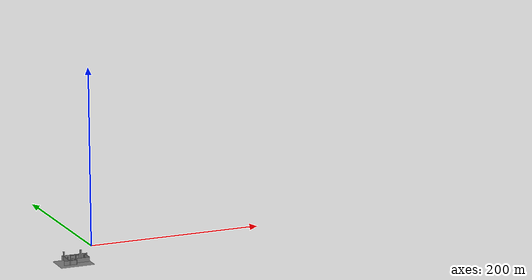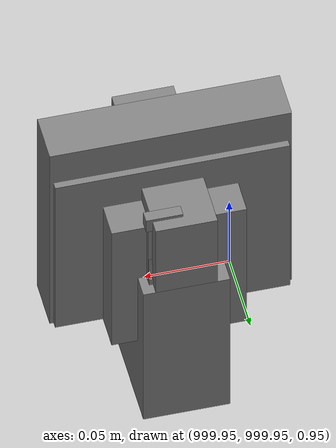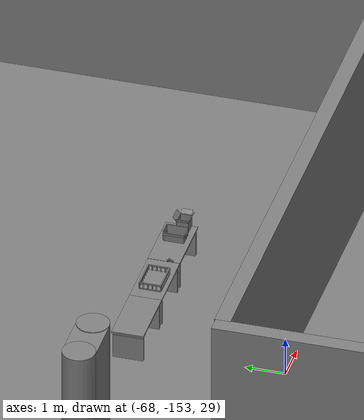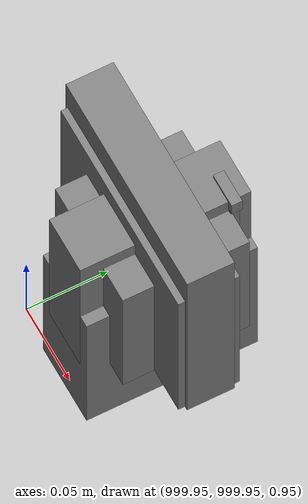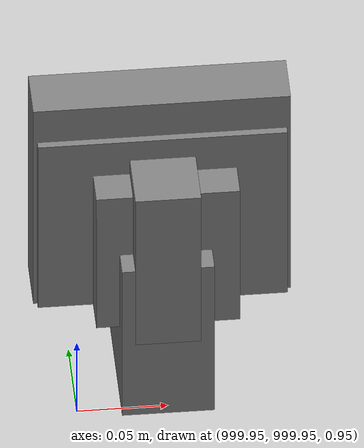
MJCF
<mujoco>
    <option gravity="0.000000000 0.000000000 -9.810000420" timestep="0.0049999999" integrator="implicitfast" density="1.225" viscosity="1.8000001e-05" noslip_iterations="10" iterations="100" sdf_iterations="50">
        <flag multiccd="disable"/>
    </option>
    <size memory="1000M"/>
    <compiler coordinate="local"/>
    <worldbody>
        <light cutoff="30" pos="0 1 1" dir="0 -1 -2"/>
        <light cutoff="30" pos="0 -1 1" dir="0 1 -2"/>
        <body pos="-65.904365540 -148.908370972 31.165357590" euler="139.655059814 -7.097862720 -170.416824341" mocap="true" name="spotlight5_SpotLight"/>
        <body pos="1000.000000000 1000.000000000 1.000000000" euler="0.000011953 0.000005123 -179.999984741" name="openloong_gripper_2f85_fix_base_usda_intel_box">
            <geom contype="1" conaffinity="1" density="1000" type="box" material="" rgba="0.500000000 0.500000000 0.500000000 1.000000000" solimp="0.899999976 0.949999988 0.001000000" friction="1.000000000 0.005000000 0.000100000" solref="0.020000000 1.000000000" margin="0" condim="3" group="0" pos="0.000000000 -0.000067139 0.000082284" quat="0.707106709 0.000000225 0.000000253 0.707106650" size="0.052800003 0.025300000 0.052800003" name="openloong_gripper_2f85_fix_base_usda_geom_E0627160_66A1_4165_9C7A_EFB4F5009992"/>
            <freejoint name="openloong_gripper_2f85_fix_base_usda_intel_box_joint"/>
            <site size="0.005000000 0.005000000 0.005000000" rgba="0.500000000 0.500000000 0.500000000 1.000000000" pos="0.000000000 0.000000000 0.000000000" quat="0.999961913 0.008726500 0.000000000 0.000000000" group="0" type="sphere" name="openloong_gripper_2f85_fix_base_usda_intel_boxsite"/>
        </body>
        <body pos="-66.376373291 -149.643508911 31.162878036" euler="8.166824341 -76.170822144 87.800506592" mocap="true" name="spotlight1_SpotLight"/>
        <body pos="1000.000000000 999.999938965 1.000000000" euler="0.000000000 0.000000000 180.000000000" name="openloong_gripper_2f85_fix_base_usda_intelcore_i5">
            <geom contype="1" conaffinity="1" density="1000" type="box" material="" rgba="0.500000000 0.500000000 0.500000000 1.000000000" solimp="0.899999976 0.949999988 0.001000000" friction="1.000000000 0.005000000 0.000100000" solref="0.020000000 1.000000000" margin="0" condim="3" group="0" pos="0.000000000 0.000000000 0.051722717" quat="0.707106709 0.000000000 0.000000000 -0.707106769" size="0.052800000 0.018080002 0.052800000" name="openloong_gripper_2f85_fix_base_usda_geom_9F7D957F_D0EF_4EA3_AD6A_683522D89A6E"/>
            <freejoint name="openloong_gripper_2f85_fix_base_usda_intelcore_i5_joint"/>
            <site size="0.005000000 0.005000000 0.005000000" rgba="0.500000000 0.500000000 0.500000000 1.000000000" pos="0.000000000 0.000000000 0.000000000" quat="0.999961913 0.008726534 0.000000000 0.000000000" group="0" type="sphere" name="openloong_gripper_2f85_fix_base_usda_intelcore_i5site"/>
        </body>
        <body pos="1000.000000000 1000.000000000 1.000000000" euler="0.000000000 0.000000000 180.000000000" name="openloong_gripper_2f85_fix_base_usda_wifi_box">
            <geom contype="1" conaffinity="1" density="1000" type="box" material="" rgba="0.500000000 0.500000000 0.500000000 1.000000000" solimp="0.899999976 0.949999988 0.001000000" friction="1.000000000 0.005000000 0.000100000" solref="0.020000000 1.000000000" margin="0" condim="3" group="0" pos="0.000000000 0.000000000 0.058978677" quat="0.000000000 0.000000047 0.000000000 1.000000000" size="0.068499997 0.018999999 0.059000000" name="openloong_gripper_2f85_fix_base_usda_geom_15D3E4EA_2C40_428D_A773_D26DF983CC55"/>
            <freejoint name="openloong_gripper_2f85_fix_base_usda_wifi_box_joint"/>
            <site size="0.005000000 0.005000000 0.005000000" rgba="0.500000000 0.500000000 0.500000000 1.000000000" pos="0.000000000 0.000000000 0.000000000" quat="0.999961913 0.008726500 0.000000000 0.000000000" group="0" type="sphere" name="openloong_gripper_2f85_fix_base_usda_wifi_boxsite"/>
        </body>
        <body pos="1000.000000000 1000.000000000 1.000000000" euler="0.000000000 0.000000000 180.000000000" name="openloong_gripper_2f85_fix_base_usda_cpu_fan">
            <geom contype="1" conaffinity="1" density="1000" type="box" material="" rgba="0.500000000 0.500000000 0.500000000 1.000000000" solimp="0.899999976 0.949999988 0.001000000" friction="1.000000000 0.005000000 0.000100000" solref="0.020000000 1.000000000" margin="0" condim="3" group="0" pos="0.000000000 0.000000000 0.070034981" quat="0.000000000 0.000000000 0.000000000 1.000000000" size="0.070700005 0.014699999 0.070700005" name="openloong_gripper_2f85_fix_base_usda_geom_4B51DCAC_9744_4716_ACFC_69FDA6F95BFC"/>
            <freejoint name="openloong_gripper_2f85_fix_base_usda_cpu_fan_joint"/>
            <site size="0.005000000 0.005000000 0.005000000" rgba="0.500000000 0.500000000 0.500000000 1.000000000" pos="0.000000000 0.000000000 0.000000000" quat="0.999961913 0.008726535 0.000000000 0.000000000" group="0" type="sphere" name="openloong_gripper_2f85_fix_base_usda_cpu_fancsite"/>
        </body>
        <body pos="-66.344306946 -149.376831055 31.168897629" euler="-23.673309326 -80.864585876 86.288536072" mocap="true" name="spotlight3_SpotLight"/>
        <body pos="1000.000000000 1000.000000000 1.000000000" euler="0.000000000 0.000000000 180.000000000" name="openloong_gripper_2f85_fix_base_usda_battery_01">
            <geom contype="1" conaffinity="1" density="1000" type="box" material="" rgba="0.500000000 0.500000000 0.500000000 1.000000000" solimp="0.899999976 0.949999988 0.001000000" friction="1.000000000 0.005000000 0.000100000" solref="0.020000000 1.000000000" margin="0" condim="3" group="0" pos="-0.011123657 -0.041940309 0.101691343" quat="1.000000000 0.000000000 0.000000000 0.000000000" size="0.010800000 0.003375000 0.004725000" name="openloong_gripper_2f85_fix_base_usda_geom_4F9661FD_D397_4B7A_AFD2_BF051C377DCA"/>
            <geom contype="1" conaffinity="1" density="1000" type="box" material="" rgba="0.500000000 0.500000000 0.500000000 1.000000000" solimp="0.899999976 0.949999988 0.001000000" friction="1.000000000 0.005000000 0.000100000" solref="0.020000000 1.000000000" margin="0" condim="3" group="0" pos="-0.010876465 -0.044247437 0.047066893" quat="0.998702705 -0.050920475 0.000000000 0.000000000" size="0.009450001 0.002700000 0.024975000" name="openloong_gripper_2f85_fix_base_usda_geom_F5FBCE12_A5CB_41A5_BD28_D70BBBB65049"/>
            <geom contype="1" conaffinity="1" density="1000" type="box" material="" rgba="0.500000000 0.500000000 0.500000000 1.000000000" solimp="0.899999976 0.949999988 0.001000000" friction="1.000000000 0.005000000 0.000100000" solref="0.020000000 1.000000000" margin="0" condim="3" group="0" pos="-0.001235962 -0.000659180 0.047381196" quat="1.000000000 0.000000000 0.000000000 0.000000000" size="0.039420001 0.039150000 0.047250003" name="openloong_gripper_2f85_fix_base_usda_geom_4D9DDA72_9ADA_48EC_8F45_135FE0B0D844"/>
            <geom contype="1" conaffinity="1" density="1000" type="box" material="" rgba="0.500000000 0.500000000 0.500000000 1.000000000" solimp="0.899999976 0.949999988 0.001000000" friction="1.000000000 0.005000000 0.000100000" solref="0.020000000 1.000000000" margin="0" condim="3" group="0" pos="-0.010876465 -0.039138794 0.009851727" quat="1.000000000 0.000000000 0.000000000 0.000000000" size="0.009450001 0.010800000 0.013500000" name="openloong_gripper_2f85_fix_base_usda_geom_F456F402_57BF_4FC1_B407_4AF26A1AC2D3"/>
            <geom contype="1" conaffinity="1" density="1000" type="box" material="" rgba="0.500000000 0.500000000 0.500000000 1.000000000" solimp="0.899999976 0.949999988 0.001000000" friction="1.000000000 0.005000000 0.000100000" solref="0.020000000 1.000000000" margin="0" condim="3" group="0" pos="-0.010876465 -0.041528322 0.071508206" quat="1.000000000 0.000000000 0.000000000 0.000000000" size="0.009450001 0.002700000 0.027000001" name="openloong_gripper_2f85_fix_base_usda_geom_48295946_0D3D_4BCA_B746_88A0767AA91D"/>
            <freejoint name="openloong_gripper_2f85_fix_base_usda_battery_01_joint"/>
            <site size="0.005000000 0.005000000 0.005000000" rgba="0.500000000 0.500000000 0.500000000 1.000000000" pos="0.000000000 0.000000000 0.000000000" quat="0.999961913 0.008726500 0.000000000 0.000000000" group="0" type="sphere" name="openloong_gripper_2f85_fix_base_usda_battery_01site"/>
        </body>
        <body pos="-64.866622925 -149.383972168 30.183746338" euler="89.999984741 89.999946594 0.000000000" name="openloong_gripper_2f85_fix_base_usda_bluebox_01">
            <geom contype="1" conaffinity="1" density="1000" type="box" material="" rgba="0.500000000 0.500000000 0.500000000 1.000000000" solimp="0.899999976 0.949999988 0.001000000" friction="1.000000000 0.005000000 0.000100000" solref="0.020000000 1.000000000" margin="0" condim="3" group="0" pos="0.276580811 0.187225342 0.000068665" quat="0.707106948 0.000077471 0.707106352 0.000077486" size="0.100000001 0.057999998 0.010000000" name="openloong_gripper_2f85_fix_base_usda_geom_62CE89A6_8C69_49E7_AB64_E6A167003504"/>
            <geom contype="1" conaffinity="1" density="1000" type="box" material="" rgba="0.500000000 0.500000000 0.500000000 1.000000000" solimp="0.899999976 0.949999988 0.001000000" friction="1.000000000 0.005000000 0.000100000" solref="0.020000000 1.000000000" margin="0" condim="3" group="0" pos="0.000000000 0.002883911 0.000000000" quat="0.999999881 0.000000000 0.000000000 0.000000000" size="0.254000008 0.003000000 0.172000006" name="openloong_gripper_2f85_fix_base_usda_geom_EC8A007E_9762_4AFB_993E_DEB5D8010D44"/>
            <geom contype="1" conaffinity="1" density="1000" type="box" material="" rgba="0.500000000 0.500000000 0.500000000 1.000000000" solimp="0.899999976 0.949999988 0.001000000" friction="1.000000000 0.005000000 0.000100000" solref="0.020000000 1.000000000" margin="0" condim="3" group="0" pos="0.000000000 0.124874115 0.173484802" quat="0.999796331 0.020176515 -0.000000015 0.000000030" size="0.259999990 0.119999997 0.007000000" name="openloong_gripper_2f85_fix_base_usda_geom_D5C36B48_1CE8_4A1D_A828_2F1DF8A2A22D"/>
            <geom contype="1" conaffinity="1" density="1000" type="box" material="" rgba="0.500000000 0.500000000 0.500000000 1.000000000" solimp="0.899999976 0.949999988 0.001000000" friction="1.000000000 0.005000000 0.000100000" solref="0.020000000 1.000000000" margin="0" condim="3" group="0" pos="0.000000000 0.124874115 -0.173469543" quat="0.999796331 -0.020176545 -0.000000015 0.000000000" size="0.259999990 0.119999997 0.007000000" name="openloong_gripper_2f85_fix_base_usda_geom_BC92B2DF_8BA0_48D8_8651_77AEAF72618E"/>
            <geom contype="1" conaffinity="1" density="1000" type="box" material="" rgba="0.500000000 0.500000000 0.500000000 1.000000000" solimp="0.899999976 0.949999988 0.001000000" friction="1.000000000 0.005000000 0.000100000" solref="0.020000000 1.000000000" margin="0" condim="3" group="0" pos="0.000000000 0.214008331 0.188980103" quat="0.999912977 0.013176724 0.000000015 0.000000000" size="0.259999990 0.029999999 0.012500000" name="openloong_gripper_2f85_fix_base_usda_geom_74E1D772_089D_44BC_9593_E29A7BE4DC4D"/>
            <geom contype="1" conaffinity="1" density="1000" type="box" material="" rgba="0.500000000 0.500000000 0.500000000 1.000000000" solimp="0.899999976 0.949999988 0.001000000" friction="1.000000000 0.005000000 0.000100000" solref="0.020000000 1.000000000" margin="0" condim="3" group="0" pos="-0.258361816 0.125289917 0.001876831" quat="0.702796936 -0.020792112 0.710783124 0.020769298" size="0.189999998 0.119999997 0.009000000" name="openloong_gripper_2f85_fix_base_usda_geom_D6E6AB6F_A6A8_4117_A16B_2F6C5016F89A"/>
            <geom contype="1" conaffinity="1" density="1000" type="box" material="" rgba="0.500000000 0.500000000 0.500000000 1.000000000" solimp="0.899999976 0.949999988 0.001000000" friction="1.000000000 0.005000000 0.000100000" solref="0.020000000 1.000000000" margin="0" condim="3" group="0" pos="0.000000000 0.214008331 -0.188980103" quat="0.999912977 -0.013176769 0.000000030 0.000000015" size="0.259999990 0.029999999 0.012500000" name="openloong_gripper_2f85_fix_base_usda_geom_0631F0C2_89E4_4FDB_882A_3FB07B83D6EA"/>
            <geom contype="1" conaffinity="1" density="1000" type="box" material="" rgba="0.500000000 0.500000000 0.500000000 1.000000000" solimp="0.899999976 0.949999988 0.001000000" friction="1.000000000 0.005000000 0.000100000" solref="0.020000000 1.000000000" margin="0" condim="3" group="0" pos="-0.276611328 0.187225342 0.000068665" quat="0.707106650 0.000077441 0.707106709 0.000077456" size="0.100000001 0.057999998 0.010000000" name="openloong_gripper_2f85_fix_base_usda_geom_E0F84528_2372_44A8_8C21_A29EBD37AA8E"/>
            <geom contype="1" conaffinity="1" density="1000" type="box" material="" rgba="0.500000000 0.500000000 0.500000000 1.000000000" solimp="0.899999976 0.949999988 0.001000000" friction="1.000000000 0.005000000 0.000100000" solref="0.020000000 1.000000000" margin="0" condim="3" group="0" pos="0.258331299 0.125289917 0.001876831" quat="0.702851415 0.018856421 0.710823774 -0.019329369" size="0.189999998 0.119999997 0.009000000" name="openloong_gripper_2f85_fix_base_usda_geom_509D1474_FF8D_41CA_A616_9253533BDF1B"/>
            <freejoint name="openloong_gripper_2f85_fix_base_usda_bluebox_01_joint"/>
            <site size="0.005000000 0.005000000 0.005000000" rgba="0.500000000 0.500000000 0.500000000 1.000000000" pos="0.000000000 0.000000000 0.000000000" quat="0.999961913 0.008726534 0.000000000 0.000000000" group="0" type="sphere" name="openloong_gripper_2f85_fix_base_usda_bluebox_01site"/>
        </body>
        <body pos="-64.496299744 -149.491867065 30.235729218" euler="0.000000000 0.000000000 89.999946594" name="openloong_gripper_2f85_fix_base_usda_cardboardbox_01">
            <geom contype="1" conaffinity="1" density="1000" type="box" material="" rgba="0.500000000 0.500000000 0.500000000 1.000000000" solimp="0.899999976 0.949999988 0.001000000" friction="1.000000000 0.005000000 0.000100000" solref="0.020000000 1.000000000" margin="0" condim="3" group="0" pos="-0.003166199 -0.004086494 0.005052090" quat="1.000000000 0.000000000 0.000000000 0.000000000" size="0.142499998 0.177500010 0.005000000" name="openloong_gripper_2f85_fix_base_usda_geom_A46B871E_0093_480A_9BF0_A45564CE8FD1"/>
            <geom contype="1" conaffinity="1" density="1000" type="box" material="" rgba="0.500000000 0.500000000 0.500000000 1.000000000" solimp="0.899999976 0.949999988 0.001000000" friction="1.000000000 0.005000000 0.000100000" solref="0.020000000 1.000000000" margin="0" condim="3" group="0" pos="-0.003166199 0.170316696 0.150570869" quat="1.000000000 0.000000000 0.000000000 0.000000000" size="0.142499998 0.005000000 0.149999991" name="openloong_gripper_2f85_fix_base_usda_geom_9C2C655F_EDD5_4C00_853F_AC80F2ABA279"/>
            <geom contype="1" conaffinity="1" density="1000" type="box" material="" rgba="0.500000000 0.500000000 0.500000000 1.000000000" solimp="0.899999976 0.949999988 0.001000000" friction="1.000000000 0.005000000 0.000100000" solref="0.020000000 1.000000000" margin="0" condim="3" group="0" pos="-0.147399902 -0.005307198 0.150570869" quat="1.000000000 0.000000000 0.000000000 0.000000000" size="0.005000000 0.177500010 0.149999991" name="openloong_gripper_2f85_fix_base_usda_geom_77FB940D_6747_4DBB_A33B_81A04E5D55BC"/>
            <geom contype="1" conaffinity="1" density="1000" type="box" material="" rgba="0.500000000 0.500000000 0.500000000 1.000000000" solimp="0.899999976 0.949999988 0.001000000" friction="1.000000000 0.005000000 0.000100000" solref="0.020000000 1.000000000" margin="0" condim="3" group="0" pos="0.140275955 -0.005307198 0.150570869" quat="1.000000000 0.000000000 0.000000000 0.000000000" size="0.005000000 0.177500010 0.149999991" name="openloong_gripper_2f85_fix_base_usda_geom_CF7CBC9F_591A_49FA_8567_8C919EE4770C"/>
            <geom contype="1" conaffinity="1" density="1000" type="box" material="" rgba="0.500000000 0.500000000 0.500000000 1.000000000" solimp="0.899999976 0.949999988 0.001000000" friction="1.000000000 0.005000000 0.000100000" solref="0.020000000 1.000000000" margin="0" condim="3" group="0" pos="-0.003166199 -0.181550980 0.150570869" quat="1.000000000 0.000000000 0.000000000 0.000000000" size="0.142499998 0.005000000 0.149999991" name="openloong_gripper_2f85_fix_base_usda_geom_AA8A4597_B52D_47F7_B3D0_D8116CB3A62D"/>
            <freejoint name="openloong_gripper_2f85_fix_base_usda_cardboardbox_01_joint"/>
            <site size="0.005000000 0.005000000 0.005000000" rgba="0.500000000 0.500000000 0.500000000 1.000000000" pos="0.000000000 0.000000000 0.000000000" quat="0.999961913 0.008726535 0.000000000 0.000000000" group="0" type="sphere" name="openloong_gripper_2f85_fix_base_usda_site_E63FE358_8ED1_4A1A_BCC0_A73C9ED509A7"/>
            <body pos="0.139160156 -0.004048347 0.301930904" euler="-179.999954224 49.383502960 179.999954224" name="openloong_gripper_2f85_fix_base_usda_A1_006">
                <geom contype="1" conaffinity="1" density="1000" type="box" material="" rgba="0.500000000 0.500000000 0.500000000 1.000000000" solimp="0.899999976 0.949999988 0.001000000" friction="1.000000000 0.005000000 0.000100000" solref="0.020000000 1.000000000" margin="0" condim="3" group="0" pos="-0.071587563 0.000009537 0.001745224" quat="0.999999881 0.000000000 0.000000000 0.000000000" size="0.071249999 0.179999992 0.002500000" name="openloong_gripper_2f85_fix_base_usda_geom_89397EC3_603D_4A02_BBAD_B159C5FCB006"/>
                <joint armature="0" stiffness="0.07" damping="0.0099999998" axis="0.000000 1.000000 0.000000" type="hinge" name="openloong_gripper_2f85_fix_base_usda_A1_006"/>
            </body>
            <body pos="-0.145902634 -0.004086494 0.301938057" euler="-180.000000000 -60.000011444 -180.000000000" name="openloong_gripper_2f85_fix_base_usda_A2_006">
                <geom contype="1" conaffinity="1" density="1000" type="box" material="" rgba="0.500000000 0.500000000 0.500000000 1.000000000" solimp="0.899999976 0.949999988 0.001000000" friction="1.000000000 0.005000000 0.000100000" solref="0.020000000 1.000000000" margin="0" condim="3" group="0" pos="0.071268082 0.000009537 0.002717972" quat="0.000002921 0.000000000 -0.000000030 0.999999881" size="0.071249999 0.179999992 0.002500000" name="openloong_gripper_2f85_fix_base_usda_geom_8DD26AEB_7F55_47B4_8A5A_90EB1158E7F3"/>
                <joint armature="0" stiffness="0.07" damping="0.0099999998" axis="0.000000 1.000000 0.000000" type="hinge" name="openloong_gripper_2f85_fix_base_usda_A2_006"/>
            </body>
            <body pos="-0.003385544 0.175991058 0.301930904" euler="-125.858116150 -0.000004561 0.000002331" name="openloong_gripper_2f85_fix_base_usda_B2_006">
                <geom contype="1" conaffinity="1" density="1000" type="box" material="" rgba="0.500000000 0.500000000 0.500000000 1.000000000" solimp="0.899999976 0.949999988 0.001000000" friction="1.000000000 0.005000000 0.000100000" solref="0.020000000 1.000000000" margin="0" condim="3" group="0" pos="0.000009537 -0.070939064 -0.002470016" quat="0.999614120 0.027776197 -0.000000015 0.000000030" size="0.137500003 0.064999998 0.005000000" name="openloong_gripper_2f85_fix_base_usda_geom_C379F9DC_9F51_425D_8CE0_08202C694BB4"/>
                <joint armature="0" stiffness="0.07" damping="0.0099999998" axis="1.000000 0.000000 0.000000" type="hinge" name="openloong_gripper_2f85_fix_base_usda_B2_006"/>
            </body>
            <body pos="-0.003385544 -0.184140205 0.301938057" euler="147.805557251 0.000000000 0.000000000" name="openloong_gripper_2f85_fix_base_usda_B1_006">
                <geom contype="1" conaffinity="1" density="1000" type="box" material="" rgba="0.500000000 0.500000000 0.500000000 1.000000000" solimp="0.899999976 0.949999988 0.001000000" friction="1.000000000 0.005000000 0.000100000" solref="0.020000000 1.000000000" margin="0" condim="3" group="0" pos="-0.000028610 0.070202351 -0.002703667" quat="0.999614179 -0.027776167 0.000000000 0.000000000" size="0.137500003 0.064999998 0.005000000" name="openloong_gripper_2f85_fix_base_usda_geom_DC51903C_DFD6_4B8E_A7C4_EDC34687B495"/>
                <joint armature="0" stiffness="0.07" damping="0.0099999998" axis="1.000000 0.000000 0.000000" type="hinge" name="openloong_gripper_2f85_fix_base_usda_B1_006"/>
            </body>
        </body>
        <body pos="-65.882858276 -149.481979370 30.229999542" euler="-64.487716675 0.000000000 0.000000000" name="openloong_gripper_2f85_fix_base_usda_Barcode">
            <geom contype="1" conaffinity="1" density="1000" type="box" material="" rgba="0.500000000 0.500000000 0.500000000 1.000000000" solimp="0.899999976 0.949999988 0.001000000" friction="1.000000000 0.005000000 0.000100000" solref="0.020000000 1.000000000" margin="0" condim="3" group="0" pos="0.000000000 0.013038635 0.001419067" quat="0.000000000 0.000000000 0.000000000 1.000000119" size="0.034000002 0.010000000 0.017999999" name="openloong_gripper_2f85_fix_base_usda_geom_E24B472D_DD2A_4A99_AEC1_9C1E32146A96"/>
            <geom contype="1" conaffinity="1" density="1000" type="box" material="" rgba="0.500000000 0.500000000 0.500000000 1.000000000" solimp="0.899999976 0.949999988 0.001000000" friction="1.000000000 0.005000000 0.000100000" solref="0.020000000 1.000000000" margin="0" condim="3" group="0" pos="0.000000000 -0.035301208 -0.007095337" quat="0.000000000 0.000000000 -0.043619365 0.999048233" size="0.028999999 0.010000000 0.020000000" name="openloong_gripper_2f85_fix_base_usda_geom_3C0FF8A2_BB04_40BB_BF50_277F42C51339"/>
            <geom contype="1" conaffinity="1" density="1000" type="box" material="" rgba="0.500000000 0.500000000 0.500000000 1.000000000" solimp="0.899999976 0.949999988 0.001000000" friction="1.000000000 0.005000000 0.000100000" solref="0.020000000 1.000000000" margin="0" condim="3" group="0" pos="0.000000000 -0.043411255 -0.011749268" quat="0.922262907 0.386563420 0.000000000 0.000000000" size="0.026000001 0.010000000 0.020000000" name="openloong_gripper_2f85_fix_base_usda_geom_871A53B3_D5DA_40C7_89BA_DB6979C694BB"/>
            <geom contype="1" conaffinity="1" density="1000" type="box" material="" rgba="0.500000000 0.500000000 0.500000000 1.000000000" solimp="0.899999976 0.949999988 0.001000000" friction="1.000000000 0.005000000 0.000100000" solref="0.020000000 1.000000000" margin="0" condim="3" group="0" pos="0.000000000 -0.016967773 -0.031860352" quat="0.000000000 0.000000000 0.000000000 1.000000119" size="0.008000000 0.010000000 0.013000000" name="openloong_gripper_2f85_fix_base_usda_geom_35C189F1_6574_43BF_87F4_366D2FAA628B"/>
            <geom contype="1" conaffinity="1" density="1000" type="box" material="" rgba="0.500000000 0.500000000 0.500000000 1.000000000" solimp="0.899999976 0.949999988 0.001000000" friction="1.000000000 0.005000000 0.000100000" solref="0.020000000 1.000000000" margin="0" condim="3" group="0" pos="0.000000000 -0.001869202 0.000312805" quat="0.953716993 0.300705761 0.000000000 0.000000000" size="0.032000002 0.010000000 0.018999999" name="openloong_gripper_2f85_fix_base_usda_geom_27D333BF_5427_4028_A8BE_A28F2A3FAAEE"/>
            <geom contype="1" conaffinity="1" density="1000" type="box" material="" rgba="0.500000000 0.500000000 0.500000000 1.000000000" solimp="0.899999976 0.949999988 0.001000000" friction="1.000000000 0.005000000 0.000100000" solref="0.020000000 1.000000000" margin="0" condim="3" group="0" pos="0.000000000 -0.019531250 -0.003173828" quat="0.953716993 0.300705761 0.000000000 0.000000000" size="0.030999999 0.010000000 0.020000000" name="openloong_gripper_2f85_fix_base_usda_geom_74123192_0D7A_4BF5_9F58_785C2BF212CE"/>
            <geom contype="1" conaffinity="1" density="1000" type="box" material="" rgba="0.500000000 0.500000000 0.500000000 1.000000000" solimp="0.899999976 0.949999988 0.001000000" friction="1.000000000 0.005000000 0.000100000" solref="0.020000000 1.000000000" margin="0" condim="3" group="0" pos="0.000000000 -0.035301208 -0.007095337" quat="0.953716993 0.300705761 0.000000000 0.000000000" size="0.028999999 0.010000000 0.020000000" name="openloong_gripper_2f85_fix_base_usda_geom_8EA3984D_1FCE_433E_8AA5_2E53284A71B6"/>
            <geom contype="1" conaffinity="1" density="1000" type="box" material="" rgba="0.500000000 0.500000000 0.500000000 1.000000000" solimp="0.899999976 0.949999988 0.001000000" friction="1.000000000 0.005000000 0.000100000" solref="0.020000000 1.000000000" margin="0" condim="3" group="0" pos="0.000000000 -0.042617798 -0.071121216" quat="0.000000000 0.000000000 0.000000000 1.000000119" size="0.013000000 0.021000000 0.059999999" name="openloong_gripper_2f85_fix_base_usda_geom_693A6217_28E9_4FAB_98C4_0EC786D49ED4"/>
            <freejoint name="openloong_gripper_2f85_fix_base_usda_Barcode_joint"/>
            <site size="0.005000000 0.005000000 0.005000000" rgba="0.500000000 0.500000000 0.500000000 1.000000000" pos="0.000000000 0.000000000 0.000000000" quat="1.000000000 0.000000000 0.000000000 0.000000000" group="0" type="sphere" name="openloong_gripper_2f85_fix_base_usda_Barcode_site"/>
        </body>
        <body pos="-66.745018005 -149.392349243 30.184000015" euler="0.000000000 0.000000000 89.999946594" name="[22332296458419]_Basket_01">
            <geom contype="1" conaffinity="1" density="1000" type="box" material="" rgba="0.500000000 0.500000000 0.500000000 1.000000000" solimp="0.899999976 0.949999988 0.001000000" friction="1.000000000 0.005000000 0.000100000" solref="0.020000000 1.000000000" margin="0" condim="3" group="0" pos="-0.052425385 0.389207840 0.089787483" quat="0.707107008 0.000000000 0.000000000 0.707106411" size="0.014249999 0.014249999 0.059999999" name="[22332296458419]_geom_546A251C_8FF1_4963_BC43_5C76BD6EC312"/>
            <geom contype="1" conaffinity="1" density="1000" type="box" material="" rgba="0.500000000 0.500000000 0.500000000 1.000000000" solimp="0.899999976 0.949999988 0.001000000" friction="1.000000000 0.005000000 0.000100000" solref="0.020000000 1.000000000" margin="0" condim="3" group="0" pos="0.264015198 -0.133043289 0.089787483" quat="0.707107008 0.000000000 0.000000000 0.707106411" size="0.014249999 0.014249999 0.059999999" name="[22332296458419]_geom_EAAE3C1C_6A88_41F9_8042_2BF3AB88D034"/>
            <geom contype="1" conaffinity="1" density="1000" type="box" material="" rgba="0.500000000 0.500000000 0.500000000 1.000000000" solimp="0.899999976 0.949999988 0.001000000" friction="1.000000000 0.005000000 0.000100000" solref="0.020000000 1.000000000" margin="0" condim="3" group="0" pos="-0.264015198 -0.265548706 0.089793205" quat="0.707107008 0.000000000 0.000000000 0.707106411" size="0.014249999 0.014249999 0.059999999" name="[22332296458419]_geom_5A76156E_279E_4965_8046_8A1622792777"/>
            <geom contype="1" conaffinity="1" density="1000" type="box" material="" rgba="0.500000000 0.500000000 0.500000000 1.000000000" solimp="0.899999976 0.949999988 0.001000000" friction="1.000000000 0.005000000 0.000100000" solref="0.020000000 1.000000000" margin="0" condim="3" group="0" pos="-0.160263062 -0.389322281 0.089793205" quat="0.707107008 0.000000000 0.000000000 0.707106411" size="0.014249999 0.014249999 0.059999999" name="[22332296458419]_geom_AB9B4CF4_18CC_475C_8710_01B180762234"/>
            <geom contype="1" conaffinity="1" density="1000" type="box" material="" rgba="0.500000000 0.500000000 0.500000000 1.000000000" solimp="0.899999976 0.949999988 0.001000000" friction="1.000000000 0.005000000 0.000100000" solref="0.020000000 1.000000000" margin="0" condim="3" group="0" pos="0.162265778 -0.389322281 0.089787483" quat="0.707107008 0.000000000 0.000000000 0.707106411" size="0.014249999 0.014249999 0.059999999" name="[22332296458419]_geom_C7DFF5F4_F980_4B7A_B058_A547A0E5D75F"/>
            <geom contype="1" conaffinity="1" density="1000" type="box" material="" rgba="0.500000000 0.500000000 0.500000000 1.000000000" solimp="0.899999976 0.949999988 0.001000000" friction="1.000000000 0.005000000 0.000100000" solref="0.020000000 1.000000000" margin="0" condim="3" group="0" pos="0.264015198 0.389207840 0.089787483" quat="0.707107008 0.000000000 0.000000000 0.707106411" size="0.014249999 0.014249999 0.059999999" name="[22332296458419]_geom_1166F337_A87A_43E1_AF49_31439BF8E178"/>
            <geom contype="1" conaffinity="1" density="1000" type="box" material="" rgba="0.500000000 0.500000000 0.500000000 1.000000000" solimp="0.899999976 0.949999988 0.001000000" friction="1.000000000 0.005000000 0.000100000" solref="0.020000000 1.000000000" margin="0" condim="3" group="0" pos="-0.264015198 -0.133043289 0.089793205" quat="0.707107008 0.000000000 0.000000000 0.707106411" size="0.014249999 0.014249999 0.059999999" name="[22332296458419]_geom_DAA01BF0_8C61_4B60_A1EA_B7F4B1ECEDC9"/>
            <geom contype="1" conaffinity="1" density="1000" type="box" material="" rgba="0.500000000 0.500000000 0.500000000 1.000000000" solimp="0.899999976 0.949999988 0.001000000" friction="1.000000000 0.005000000 0.000100000" solref="0.020000000 1.000000000" margin="0" condim="3" group="0" pos="-0.264026642 0.269256592 0.089793205" quat="0.707107008 0.000000000 0.000000000 0.707106411" size="0.014249999 0.014249999 0.059999999" name="[22332296458419]_geom_B49EE928_F8F7_4CB1_BEB8_D2DEC73DF9F0"/>
            <geom contype="1" conaffinity="1" density="1000" type="box" material="" rgba="0.500000000 0.500000000 0.500000000 1.000000000" solimp="0.899999976 0.949999988 0.001000000" friction="1.000000000 0.005000000 0.000100000" solref="0.020000000 1.000000000" margin="0" condim="3" group="0" pos="0.054462433 0.389207840 0.089787483" quat="0.707107008 0.000000000 0.000000000 0.707106411" size="0.014249999 0.014249999 0.059999999" name="[22332296458419]_geom_692F5565_F480_4CF1_8928_33117857C73C"/>
            <geom contype="1" conaffinity="1" density="1000" type="box" material="" rgba="0.500000000 0.500000000 0.500000000 1.000000000" solimp="0.899999976 0.949999988 0.001000000" friction="1.000000000 0.005000000 0.000100000" solref="0.020000000 1.000000000" margin="0" condim="3" group="0" pos="0.054462433 -0.389322281 0.089787483" quat="0.707107008 0.000000000 0.000000000 0.707106411" size="0.014249999 0.014249999 0.059999999" name="[22332296458419]_geom_C779473E_F3BF_4685_AFAB_10832F7D9E2F"/>
            <geom contype="1" conaffinity="1" density="1000" type="box" material="" rgba="0.500000000 0.500000000 0.500000000 1.000000000" solimp="0.899999976 0.949999988 0.001000000" friction="1.000000000 0.005000000 0.000100000" solref="0.020000000 1.000000000" margin="0" condim="3" group="0" pos="0.264015198 0.269256592 0.089793205" quat="0.707107008 0.000000000 0.000000000 0.707106411" size="0.014249999 0.014249999 0.059999999" name="[22332296458419]_geom_05A877E4_D43C_4D29_AE5B_CDABA0E4C0B5"/>
            <geom contype="1" conaffinity="1" density="1000" type="box" material="" rgba="0.500000000 0.500000000 0.500000000 1.000000000" solimp="0.899999976 0.949999988 0.001000000" friction="1.000000000 0.005000000 0.000100000" solref="0.020000000 1.000000000" margin="0" condim="3" group="0" pos="0.264015198 -0.389322281 0.089787483" quat="0.707107008 0.000000000 0.000000000 0.707106411" size="0.014249999 0.014249999 0.059999999" name="[22332296458419]_geom_2E4067F2_A74D_4BC8_8E23_2F764CDBD890"/>
            <geom contype="1" conaffinity="1" density="1000" type="box" material="" rgba="0.500000000 0.500000000 0.500000000 1.000000000" solimp="0.899999976 0.949999988 0.001000000" friction="1.000000000 0.005000000 0.000100000" solref="0.020000000 1.000000000" margin="0" condim="3" group="0" pos="0.000000000 0.000000000 0.015998840" quat="0.707107008 0.000000000 0.000000000 0.707106411" size="0.403499991 0.279000014 0.015750000" name="[22332296458419]_geom_7AC00AE3_1D5E_4F9A_8D25_5773D90BBE7C"/>
            <geom contype="1" conaffinity="1" density="1000" type="box" material="" rgba="0.500000000 0.500000000 0.500000000 1.000000000" solimp="0.899999976 0.949999988 0.001000000" friction="1.000000000 0.005000000 0.000100000" solref="0.020000000 1.000000000" margin="0" condim="3" group="0" pos="0.000000000 -0.389476776 0.163619041" quat="0.707107008 0.000000000 0.000000000 0.707106411" size="0.015000000 0.277500004 0.015750000" name="[22332296458419]_geom_602751D2_B111_4DAD_9AC6_435B8E42AC56"/>
            <geom contype="1" conaffinity="1" density="1000" type="box" material="" rgba="0.500000000 0.500000000 0.500000000 1.000000000" solimp="0.899999976 0.949999988 0.001000000" friction="1.000000000 0.005000000 0.000100000" solref="0.020000000 1.000000000" margin="0" condim="3" group="0" pos="0.162265778 0.389207840 0.089787483" quat="0.707107008 0.000000000 0.000000000 0.707106411" size="0.014249999 0.014249999 0.059999999" name="[22332296458419]_geom_2FA063D9_99E8_4100_99BD_A5996C00C3F7"/>
            <geom contype="1" conaffinity="1" density="1000" type="box" material="" rgba="0.500000000 0.500000000 0.500000000 1.000000000" solimp="0.899999976 0.949999988 0.001000000" friction="1.000000000 0.005000000 0.000100000" solref="0.020000000 1.000000000" margin="0" condim="3" group="0" pos="0.000000000 0.389471054 0.163619041" quat="0.707107008 0.000000000 0.000000000 0.707106411" size="0.015000000 0.277500004 0.015750000" name="[22332296458419]_geom_9C4BC6FD_CECD_497D_850B_861C496F3F28"/>
            <geom contype="1" conaffinity="1" density="1000" type="box" material="" rgba="0.500000000 0.500000000 0.500000000 1.000000000" solimp="0.899999976 0.949999988 0.001000000" friction="1.000000000 0.005000000 0.000100000" solref="0.020000000 1.000000000" margin="0" condim="3" group="0" pos="-0.263511658 0.000000000 0.163619041" quat="0.707107008 0.000000000 0.000000000 0.707106411" size="0.403499991 0.015000000 0.015750000" name="[22332296458419]_geom_2D773430_ADAD_4A10_B6B2_7913B8047030"/>
            <geom contype="1" conaffinity="1" density="1000" type="box" material="" rgba="0.500000000 0.500000000 0.500000000 1.000000000" solimp="0.899999976 0.949999988 0.001000000" friction="1.000000000 0.005000000 0.000100000" solref="0.020000000 1.000000000" margin="0" condim="3" group="0" pos="-0.264015198 0.141334534 0.089793205" quat="0.707107008 0.000000000 0.000000000 0.707106411" size="0.014249999 0.014249999 0.059999999" name="[22332296458419]_geom_6DA19F8A_F224_4273_B64C_1D9C08AE63EF"/>
            <geom contype="1" conaffinity="1" density="1000" type="box" material="" rgba="0.500000000 0.500000000 0.500000000 1.000000000" solimp="0.899999976 0.949999988 0.001000000" friction="1.000000000 0.005000000 0.000100000" solref="0.020000000 1.000000000" margin="0" condim="3" group="0" pos="0.264015198 -0.265548706 0.089787483" quat="0.707107008 0.000000000 0.000000000 0.707106411" size="0.014249999 0.014249999 0.059999999" name="[22332296458419]_geom_B901E0A7_67CA_45A7_9603_7E60CDAACFE1"/>
            <geom contype="1" conaffinity="1" density="1000" type="box" material="" rgba="0.500000000 0.500000000 0.500000000 1.000000000" solimp="0.899999976 0.949999988 0.001000000" friction="1.000000000 0.005000000 0.000100000" solref="0.020000000 1.000000000" margin="0" condim="3" group="0" pos="-0.160263062 0.389207840 0.089787483" quat="0.707107008 0.000000000 0.000000000 0.707106411" size="0.014249999 0.014249999 0.059999999" name="[22332296458419]_geom_4D9E286F_2F53_4A5C_83EB_C0EF939F1409"/>
            <geom contype="1" conaffinity="1" density="1000" type="box" material="" rgba="0.500000000 0.500000000 0.500000000 1.000000000" solimp="0.899999976 0.949999988 0.001000000" friction="1.000000000 0.005000000 0.000100000" solref="0.020000000 1.000000000" margin="0" condim="3" group="0" pos="-0.052425385 -0.389322281 0.089787483" quat="0.707107008 0.000000000 0.000000000 0.707106411" size="0.014249999 0.014249999 0.059999999" name="[22332296458419]_geom_95E00CB6_88F4_4E41_B18F_1FEC98F25FB7"/>
            <geom contype="1" conaffinity="1" density="1000" type="box" material="" rgba="0.500000000 0.500000000 0.500000000 1.000000000" solimp="0.899999976 0.949999988 0.001000000" friction="1.000000000 0.005000000 0.000100000" solref="0.020000000 1.000000000" margin="0" condim="3" group="0" pos="-0.264026642 -0.389322281 0.089793205" quat="0.707107008 0.000000000 0.000000000 0.707106411" size="0.014249999 0.014249999 0.059999999" name="[22332296458419]_geom_BB08DCA3_6E27_458F_B11D_423916C38A9F"/>
            <geom contype="1" conaffinity="1" density="1000" type="box" material="" rgba="0.500000000 0.500000000 0.500000000 1.000000000" solimp="0.899999976 0.949999988 0.001000000" friction="1.000000000 0.005000000 0.000100000" solref="0.020000000 1.000000000" margin="0" condim="3" group="0" pos="0.264015198 0.141334534 0.089787483" quat="0.707107008 0.000000000 0.000000000 0.707106411" size="0.014249999 0.014249999 0.059999999" name="[22332296458419]_geom_C837770C_273C_453B_9543_A9681335581D"/>
            <geom contype="1" conaffinity="1" density="1000" type="box" material="" rgba="0.500000000 0.500000000 0.500000000 1.000000000" solimp="0.899999976 0.949999988 0.001000000" friction="1.000000000 0.005000000 0.000100000" solref="0.020000000 1.000000000" margin="0" condim="3" group="0" pos="-0.264015198 0.389207840 0.089793205" quat="0.707107008 0.000000000 0.000000000 0.707106411" size="0.014249999 0.014249999 0.059999999" name="[22332296458419]_geom_FC194CDB_ADC7_4BAA_A4C7_886DEF701633"/>
            <geom contype="1" conaffinity="1" density="1000" type="box" material="" rgba="0.500000000 0.500000000 0.500000000 1.000000000" solimp="0.899999976 0.949999988 0.001000000" friction="1.000000000 0.005000000 0.000100000" solref="0.020000000 1.000000000" margin="0" condim="3" group="0" pos="0.264015198 0.004480362 0.089787483" quat="0.707107008 0.000000000 0.000000000 0.707106411" size="0.014249999 0.014249999 0.059999999" name="[22332296458419]_geom_3942A844_5283_4D35_944A_DE4F5181A5C3"/>
            <geom contype="1" conaffinity="1" density="1000" type="box" material="" rgba="0.500000000 0.500000000 0.500000000 1.000000000" solimp="0.899999976 0.949999988 0.001000000" friction="1.000000000 0.005000000 0.000100000" solref="0.020000000 1.000000000" margin="0" condim="3" group="0" pos="0.263694763 -0.000011444 0.163619041" quat="0.707107008 0.000000000 0.000000000 0.707106411" size="0.403499991 0.015000000 0.015750000" name="[22332296458419]_geom_57A90B40_B888_4E5A_8120_B65F0975BF36"/>
            <geom contype="1" conaffinity="1" density="1000" type="box" material="" rgba="0.500000000 0.500000000 0.500000000 1.000000000" solimp="0.899999976 0.949999988 0.001000000" friction="1.000000000 0.005000000 0.000100000" solref="0.020000000 1.000000000" margin="0" condim="3" group="0" pos="-0.264015198 0.004480362 0.089793205" quat="0.707107008 0.000000000 0.000000000 0.707106411" size="0.014249999 0.014249999 0.059999999" name="[22332296458419]_geom_BDA6031F_19EC_4406_B7DC_D047E0F445BE"/>
            <freejoint name="[22332296458419]_joint_D954B501_DD21_4310_A824_06FD635EB4B3"/>
        </body>
        <body pos="0.000000000 0.000000000 0.000000000" euler="0.000000000 0.000000000 0.000000000" name="Static Objects_Static Objects">
            <geom contype="1" conaffinity="1" density="1000" type="box" material="" rgba="0.500000000 0.500000000 0.500000000 1.000000000" solimp="0.899999976 0.949999988 0.001000000" friction="1.000000000 0.005000000 0.000100000" solref="0.020000000 1.000000000" margin="0" condim="3" group="0" pos="-67.544113159 -149.365814209 29.727830887" quat="0.500000417 0.499999970 0.499999553 0.499999970" size="0.381000012 0.319999993 0.041000001" name="Static Objects_geom_05F9A82E_BEA8_47ED_AE5D_7273297FAEE7"/>
            <geom contype="1" conaffinity="1" density="1000" type="box" material="" rgba="0.500000000 0.500000000 0.500000000 1.000000000" solimp="0.899999976 0.949999988 0.001000000" friction="1.000000000 0.005000000 0.000100000" solref="0.020000000 1.000000000" margin="0" condim="3" group="0" pos="-68.239501953 -149.365814209 30.086868286" quat="0.500000417 0.499999970 0.499999553 0.499999970" size="0.370999992 0.039500002 0.745000005" name="Static Objects_geom_55373937_081E_4354_AFEB_44C17D0D0C38"/>
            <geom contype="1" conaffinity="1" density="1000" type="box" material="" rgba="0.500000000 0.500000000 0.500000000 1.000000000" solimp="0.899999976 0.949999988 0.001000000" friction="1.000000000 0.005000000 0.000100000" solref="0.020000000 1.000000000" margin="0" condim="3" group="0" pos="-68.239501953 -149.365814209 30.147235870" quat="0.500000417 0.499999970 0.499999553 0.499999970" size="0.400000006 0.022000000 0.800000012" name="Static Objects_geom_7A299DC7_118D_42EB_B99B_F317613E4E01"/>
            <geom contype="1" conaffinity="1" density="1000" type="box" material="" rgba="0.500000000 0.500000000 0.500000000 1.000000000" solimp="0.899999976 0.949999988 0.001000000" friction="1.000000000 0.005000000 0.000100000" solref="0.020000000 1.000000000" margin="0" condim="3" group="0" pos="-68.934890747 -149.365814209 29.727830887" quat="0.500000417 0.499999970 0.499999553 0.499999970" size="0.381000012 0.319999993 0.041000001" name="Static Objects_geom_DCA05931_701E_4DB9_8719_618472ACEAD5"/>
            <geom contype="1" conaffinity="1" density="1000" type="box" material="" rgba="0.500000000 0.500000000 0.500000000 1.000000000" solimp="0.899999976 0.949999988 0.001000000" friction="1.000000000 0.005000000 0.000100000" solref="0.020000000 1.000000000" margin="0" condim="3" group="0" pos="-68.239501953 -149.365814209 29.561563492" quat="0.500000417 0.499999970 0.499999553 0.499999970" size="0.020000000 0.022000000 0.660000026" name="Static Objects_geom_80D43586_D9B1_4AFC_99C7_88D5B820DCA8"/>
            <geom contype="1" conaffinity="1" density="1000" type="box" material="" rgba="0.500000000 0.500000000 0.500000000 1.000000000" solimp="0.899999976 0.949999988 0.001000000" friction="1.000000000 0.005000000 0.000100000" solref="0.020000000 1.000000000" margin="0" condim="3" group="0" pos="-65.945671082 -149.365814209 29.727830887" quat="0.500000417 0.499999970 0.499999553 0.499999970" size="0.381000012 0.319999993 0.041000001" name="Static Objects_geom_1952B740_6CBC_4CEF_9C0D_E92EAF817CBA"/>
            <geom contype="1" conaffinity="1" density="1000" type="box" material="" rgba="0.500000000 0.500000000 0.500000000 1.000000000" solimp="0.899999976 0.949999988 0.001000000" friction="1.000000000 0.005000000 0.000100000" solref="0.020000000 1.000000000" margin="0" condim="3" group="0" pos="-66.641059875 -149.365814209 30.086868286" quat="0.500000417 0.499999970 0.499999553 0.499999970" size="0.370999992 0.039500002 0.745000005" name="Static Objects_geom_ABDB7521_28F3_4D31_9E5C_7765AF829483"/>
            <geom contype="1" conaffinity="1" density="1000" type="box" material="" rgba="0.500000000 0.500000000 0.500000000 1.000000000" solimp="0.899999976 0.949999988 0.001000000" friction="1.000000000 0.005000000 0.000100000" solref="0.020000000 1.000000000" margin="0" condim="3" group="0" pos="-66.641059875 -149.365814209 30.147235870" quat="0.500000417 0.499999970 0.499999553 0.499999970" size="0.400000006 0.022000000 0.800000012" name="Static Objects_geom_25C704D2_3576_4597_B74B_B0B2C21BC7B2"/>
            <geom contype="1" conaffinity="1" density="1000" type="box" material="" rgba="0.500000000 0.500000000 0.500000000 1.000000000" solimp="0.899999976 0.949999988 0.001000000" friction="1.000000000 0.005000000 0.000100000" solref="0.020000000 1.000000000" margin="0" condim="3" group="0" pos="-67.336448669 -149.365814209 29.727830887" quat="0.500000417 0.499999970 0.499999553 0.499999970" size="0.381000012 0.319999993 0.041000001" name="Static Objects_geom_508EC641_5B5C_4167_92EF_70D7C6772206"/>
            <geom contype="1" conaffinity="1" density="1000" type="box" material="" rgba="0.500000000 0.500000000 0.500000000 1.000000000" solimp="0.899999976 0.949999988 0.001000000" friction="1.000000000 0.005000000 0.000100000" solref="0.020000000 1.000000000" margin="0" condim="3" group="0" pos="-66.641059875 -149.365814209 29.561563492" quat="0.500000417 0.499999970 0.499999553 0.499999970" size="0.020000000 0.022000000 0.660000026" name="Static Objects_geom_F9232D87_466B_4F9B_A926_39EB3643B565"/>
            <geom contype="1" conaffinity="1" density="1000" type="box" material="" rgba="0.500000000 0.500000000 0.500000000 1.000000000" solimp="0.899999976 0.949999988 0.001000000" friction="1.000000000 0.005000000 0.000100000" solref="0.020000000 1.000000000" margin="0" condim="3" group="0" pos="-64.338577271 -149.365814209 29.727830887" quat="0.500000417 0.499999970 0.499999553 0.499999970" size="0.381000012 0.319999993 0.041000001" name="Static Objects_geom_1EF13352_5EBD_4182_BC6B_D2EEF5666C4D"/>
            <geom contype="1" conaffinity="1" density="1000" type="box" material="" rgba="0.500000000 0.500000000 0.500000000 1.000000000" solimp="0.899999976 0.949999988 0.001000000" friction="1.000000000 0.005000000 0.000100000" solref="0.020000000 1.000000000" margin="0" condim="3" group="0" pos="-65.033966064 -149.365814209 30.086868286" quat="0.500000417 0.499999970 0.499999553 0.499999970" size="0.370999992 0.039500002 0.745000005" name="Static Objects_geom_4E9B325D_CABD_4915_B2A5_9E029BC230EB"/>
            <geom contype="1" conaffinity="1" density="1000" type="box" material="" rgba="0.500000000 0.500000000 0.500000000 1.000000000" solimp="0.899999976 0.949999988 0.001000000" friction="1.000000000 0.005000000 0.000100000" solref="0.020000000 1.000000000" margin="0" condim="3" group="0" pos="-65.033966064 -149.365814209 30.147235870" quat="0.500000417 0.499999970 0.499999553 0.499999970" size="0.400000006 0.022000000 0.800000012" name="Static Objects_geom_36C52E93_09C8_4915_AC9A_232FCF3579CD"/>
            <geom contype="1" conaffinity="1" density="1000" type="box" material="" rgba="0.500000000 0.500000000 0.500000000 1.000000000" solimp="0.899999976 0.949999988 0.001000000" friction="1.000000000 0.005000000 0.000100000" solref="0.020000000 1.000000000" margin="0" condim="3" group="0" pos="-65.729354858 -149.365814209 29.727830887" quat="0.500000417 0.499999970 0.499999553 0.499999970" size="0.381000012 0.319999993 0.041000001" name="Static Objects_geom_63E79EA8_55CF_4B3B_9F47_CB6A1D762A10"/>
            <geom contype="1" conaffinity="1" density="1000" type="box" material="" rgba="0.500000000 0.500000000 0.500000000 1.000000000" solimp="0.899999976 0.949999988 0.001000000" friction="1.000000000 0.005000000 0.000100000" solref="0.020000000 1.000000000" margin="0" condim="3" group="0" pos="-65.033966064 -149.365814209 29.561563492" quat="0.500000417 0.499999970 0.499999553 0.499999970" size="0.020000000 0.022000000 0.660000026" name="Static Objects_geom_6DFC9359_901B_4D13_8FD7_18E068466895"/>
            <geom contype="1" conaffinity="1" density="1000" type="box" material="" rgba="0.500000000 0.500000000 0.500000000 1.000000000" solimp="0.899999976 0.949999988 0.001000000" friction="1.000000000 0.005000000 0.000100000" solref="0.020000000 1.000000000" margin="0" condim="3" group="0" pos="-61.754566193 -137.853729248 33.906845093" quat="0.707107067 0.000000000 0.000000000 0.707106471" size="0.759999990 0.759999990 4.500000000" name="Static Objects_geom_E4917476_3B47_46CD_8292_A2F7EEAAAE9A"/>
            <geom contype="1" conaffinity="1" density="1000" type="box" material="" rgba="0.500000000 0.500000000 0.500000000 1.000000000" solimp="0.899999976 0.949999988 0.001000000" friction="1.000000000 0.005000000 0.000100000" solref="0.020000000 1.000000000" margin="0" condim="3" group="0" pos="-57.511135101 -144.927108765 31.707921982" quat="1.000000000 0.000000000 0.000000000 0.000000000" size="0.200000003 8.000000000 2.299999952" name="Static Objects_geom_20D74E9E_C318_42DF_AE9A_DA9FB5212EB1"/>
            <geom contype="1" conaffinity="1" density="1000" type="box" material="" rgba="0.500000000 0.500000000 0.500000000 1.000000000" solimp="0.899999976 0.949999988 0.001000000" friction="1.000000000 0.005000000 0.000100000" solref="0.020000000 1.000000000" margin="0" condim="3" group="0" pos="-80.517646790 -157.574050903 31.688196182" quat="0.707107067 0.000000000 0.000000000 0.707106471" size="0.600000024 0.600000024 2.299999952" name="Static Objects_geom_2296612A_845A_437C_ABC1_6B35724F910F"/>
            <geom contype="1" conaffinity="1" density="1000" type="box" material="" rgba="0.500000000 0.500000000 0.500000000 1.000000000" solimp="0.899999976 0.949999988 0.001000000" friction="1.000000000 0.005000000 0.000100000" solref="0.020000000 1.000000000" margin="0" condim="3" group="0" pos="-80.711044312 -147.414932251 31.666158676" quat="1.000000000 0.000000000 0.000000000 0.000000000" size="0.200000003 10.000000000 2.299999952" name="Static Objects_geom_4F7E2627_900A_45E0_AA48_6B2F0D231D17"/>
            <geom contype="1" conaffinity="1" density="1000" type="box" material="" rgba="0.500000000 0.500000000 0.500000000 1.000000000" solimp="0.899999976 0.949999988 0.001000000" friction="1.000000000 0.005000000 0.000100000" solref="0.020000000 1.000000000" margin="0" condim="3" group="0" pos="-57.687217712 -137.434692383 31.688196182" quat="0.707107067 0.000000000 0.000000000 0.707106471" size="0.600000024 0.600000024 2.299999952" name="Static Objects_geom_23568404_27A3_415F_852A_E48060DC6942"/>
            <geom contype="1" conaffinity="1" density="1000" type="box" material="" rgba="0.500000000 0.500000000 0.500000000 1.000000000" solimp="0.899999976 0.949999988 0.001000000" friction="1.000000000 0.005000000 0.000100000" solref="0.020000000 1.000000000" margin="0" condim="3" group="0" pos="-69.537033081 -140.263229370 31.714921951" quat="0.707107067 0.000000000 0.000000000 0.707106471" size="0.759999990 4.500000000 2.299999952" name="Static Objects_geom_71692231_1C31_454B_AD11_0079A4516278"/>
            <geom contype="1" conaffinity="1" density="1000" type="box" material="" rgba="0.500000000 0.500000000 0.500000000 1.000000000" solimp="0.899999976 0.949999988 0.001000000" friction="1.000000000 0.005000000 0.000100000" solref="0.020000000 1.000000000" margin="0" condim="3" group="0" pos="-80.073638916 -137.853713989 33.906845093" quat="0.707107067 0.000000000 0.000000000 0.707106471" size="0.759999990 0.759999990 4.500000000" name="Static Objects_geom_83DE5E29_E8B0_4F38_A28A_5C60F1E9B6DD"/>
            <geom contype="1" conaffinity="1" density="1000" type="box" material="" rgba="0.500000000 0.500000000 0.500000000 1.000000000" solimp="0.899999976 0.949999988 0.001000000" friction="1.000000000 0.005000000 0.000100000" solref="0.020000000 1.000000000" margin="0" condim="3" group="0" pos="-73.406707764 -155.734664917 31.707921982" quat="1.000000000 0.000000000 0.000000000 0.000000000" size="0.200000003 3.000000000 2.299999952" name="Static Objects_geom_080BA254_F3E4_4B2E_9CEC_020011CC9824"/>
            <geom contype="1" conaffinity="1" density="1000" type="box" material="" rgba="0.500000000 0.500000000 0.500000000 1.000000000" solimp="0.899999976 0.949999988 0.001000000" friction="1.000000000 0.005000000 0.000100000" solref="0.020000000 1.000000000" margin="0" condim="3" group="0" pos="-68.497543335 -137.448257446 31.707921982" quat="0.707107067 0.000000000 0.000000000 0.707106471" size="0.200000003 14.000000000 2.299999952" name="Static Objects_geom_5E2304B2_3F7B_4DE1_87D2_797FD9ABCA80"/>
            <geom contype="1" conaffinity="1" density="1000" type="cylinder" material="" rgba="0.500000000 0.500000000 0.500000000 1.000000000" solimp="0.899999976 0.949999988 0.001000000" friction="1.000000000 0.005000000 0.000100000" solref="0.020000000 1.000000000" margin="0" condim="3" group="0" pos="-68.868522644 -142.134506226 31.711090088" quat="0.707107067 0.000000000 0.000000000 0.707106471" size="0.509999990 2.299999952 1.000000000" name="Static Objects_geom_EB2DD95A_4AC0_41B0_BBF7_31F6100DAB8A"/>
            <geom contype="1" conaffinity="1" density="1000" type="plane" material="" rgba="0.500000000 0.500000000 0.500000000 1.000000000" solimp="0.899999976 0.949999988 0.001000000" friction="1.000000000 0.005000000 0.000100000" solref="0.020000000 1.000000000" margin="0" condim="3" group="0" pos="-72.873703003 -147.131927490 29.409669876" quat="1.000000000 0.000000000 0.000000000 0.000000000" size="18.000000000 14.000000000 1.000000000" name="Static Objects_geom_870BA905_8CCC_4B86_8809_FD0D92C0CE7C"/>
            <geom contype="1" conaffinity="1" density="1000" type="box" material="" rgba="0.500000000 0.500000000 0.500000000 1.000000000" solimp="0.899999976 0.949999988 0.001000000" friction="1.000000000 0.005000000 0.000100000" solref="0.020000000 1.000000000" margin="0" condim="3" group="0" pos="-79.943580627 -157.782272339 31.707921982" quat="0.707107067 0.000000000 0.000000000 0.707106471" size="0.200000003 7.000000000 2.299999952" name="Static Objects_geom_5D96AFDF_E420_4B0D_9B59_C07C67F10386"/>
            <geom contype="1" conaffinity="1" density="1000" type="box" material="" rgba="0.500000000 0.500000000 0.500000000 1.000000000" solimp="0.899999976 0.949999988 0.001000000" friction="1.000000000 0.005000000 0.000100000" solref="0.020000000 1.000000000" margin="0" condim="3" group="0" pos="-65.421028137 -152.903442383 31.707921982" quat="0.707107067 0.000000000 0.000000000 0.707106471" size="0.200000003 7.800000191 2.299999952" name="Static Objects_geom_EC1C4D10_D9F0_4621_9D04_FB516534E84D"/>
            <geom contype="1" conaffinity="1" density="1000" type="box" material="" rgba="0.500000000 0.500000000 0.500000000 1.000000000" solimp="0.899999976 0.949999988 0.001000000" friction="1.000000000 0.005000000 0.000100000" solref="0.020000000 1.000000000" margin="0" condim="3" group="0" pos="-74.776908875 -149.964416504 31.688196182" quat="1.000000000 0.000000000 0.000000000 0.000000000" size="0.600000024 0.409999996 2.299999952" name="Static Objects_geom_11AB1AF6_15D7_4388_BE6D_08C1EE02FCB5"/>
            <geom contype="1" conaffinity="1" density="1000" type="cylinder" material="" rgba="0.500000000 0.500000000 0.500000000 1.000000000" solimp="0.899999976 0.949999988 0.001000000" friction="1.000000000 0.005000000 0.000100000" solref="0.020000000 1.000000000" margin="0" condim="3" group="0" pos="-60.161884308 -142.134506226 31.711090088" quat="0.707107067 0.000000000 0.000000000 0.707106471" size="0.509999990 2.299999952 1.000000000" name="Static Objects_geom_D081E0E7_7B94_416B_9646_DF13DDE180D0"/>
            <geom contype="1" conaffinity="1" density="1000" type="cylinder" material="" rgba="0.500000000 0.500000000 0.500000000 1.000000000" solimp="0.899999976 0.949999988 0.001000000" friction="1.000000000 0.005000000 0.000100000" solref="0.020000000 1.000000000" margin="0" condim="3" group="0" pos="-75.382453918 -149.963455200 31.711090088" quat="0.707107067 0.000000000 0.000000000 0.707106471" size="0.409999996 2.299999952 1.000000000" name="Static Objects_geom_AA3EAF49_B8F2_4E79_B71F_C67B86EFE764"/>
            <geom contype="1" conaffinity="1" density="1000" type="cylinder" material="" rgba="0.500000000 0.500000000 0.500000000 1.000000000" solimp="0.899999976 0.949999988 0.001000000" friction="1.000000000 0.005000000 0.000100000" solref="0.020000000 1.000000000" margin="0" condim="3" group="0" pos="-74.154960632 -149.963455200 31.711090088" quat="0.707107067 0.000000000 0.000000000 0.707106471" size="0.409999996 2.299999952 1.000000000" name="Static Objects_geom_B1CD8B07_B0A3_4562_82AE_BA4A1C5442E0"/>
            <geom contype="1" conaffinity="1" density="1000" type="cylinder" material="" rgba="0.500000000 0.500000000 0.500000000 1.000000000" solimp="0.899999976 0.949999988 0.001000000" friction="1.000000000 0.005000000 0.000100000" solref="0.020000000 1.000000000" margin="0" condim="3" group="0" pos="-77.566612244 -142.134506226 31.711090088" quat="0.707107067 0.000000000 0.000000000 0.707106471" size="0.509999990 2.299999952 1.000000000" name="Static Objects_geom_9FEFEC51_10C3_4892_AD15_5DC99F58889C"/>
        </body>
        <body pos="-66.291030884 -149.869689941 29.018842697" euler="0.000000000 0.000000000 89.999946594" mocap="true" name="openloong_gripper_2f85_fix_base_usda_leftHandMocap"/>
        <body pos="-66.291030884 -149.869689941 29.018842697" euler="0.000000000 0.000000000 89.999946594" mocap="true" name="openloong_gripper_2f85_fix_base_usda_rightHandMocap"/>
        <body pos="-66.291030884 -149.869689941 30.218843460" euler="0.000000000 0.000000000 89.999946594" name="openloong_gripper_2f85_fix_base_usda_base_link">
            <geom contype="1" conaffinity="1" density="1000" type="mesh" material="" rgba="0.783999979 0.783999979 0.783999979 1.000000000" solimp="0.899999976 0.949999988 0.001000000" friction="1.000000000 0.005000000 0.000100000" solref="0.020000000 1.000000000" margin="0" condim="3" group="3" mesh="base_link" pos="0.000000000 0.000000000 0.000000000" quat="1.000000000 0.000000000 0.000000000 0.000000000" size="1.000000000 1.000000000 1.000000000" name="openloong_gripper_2f85_fix_base_usda__geom_7_DE7574FE_44A0_41EB_B3A0_4922B2A5195C"/>
            <site size="0.005000000 0.005000000 0.005000000" rgba="0.500000000 0.500000000 0.500000000 1.000000000" pos="0.000000000 0.000000000 0.000000000" quat="1.000000000 0.000000000 0.000000000 0.000000000" group="0" type="sphere" name="openloong_gripper_2f85_fix_base_usda_imu"/>
            <inertial mass="22.447001" pos="-0.005664100 -0.001336700 0.238289997" diaginertia="0.374352545 0.277180195 0.220617250" quat="0.999247074 0.035235517 -0.015086859 0.006023135"/>
            <body pos="0.000000000 0.000000000 0.299997330" euler="0.000000000 0.000000000 0.000000000" name="openloong_gripper_2f85_fix_base_usda_dummy_body">
                <geom contype="1" conaffinity="1" density="1000" type="sphere" material="" rgba="0.783999979 0.783999979 0.783999979 1.000000000" solimp="0.899999976 0.949999988 0.001000000" friction="1.000000000 0.005000000 0.000100000" solref="0.020000000 1.000000000" margin="0" condim="3" group="3" pos="0.000000000 0.000000000 0.000000000" quat="1.000000000 0.000000000 0.000000000 0.000000000" size="0.010000000 0.000000000 0.000000000" name="openloong_gripper_2f85_fix_base_usda__geom_8_DD3F323C_ECD9_4D2E_8770_21E311B164E3"/>
                <joint armature="0.0099999998" stiffness="0" damping="0.1" axis="0.000000 0.000000 1.000000" type="hinge" name="openloong_gripper_2f85_fix_base_usda_dummy_joint"/>
                <site size="0.010000000 0.005000000 0.005000000" rgba="0.500000000 0.500000000 0.500000000 1.000000000" pos="0.000000000 0.000000000 0.000000000" quat="1.000000000 0.000000000 0.000000000 0.000000000" group="3" type="sphere" name="openloong_gripper_2f85_fix_base_usda_dummy_site"/>
            </body>
            <body pos="0.009002686 0.000000000 0.406400681" euler="0.000000000 0.000000000 0.000000000" name="openloong_gripper_2f85_fix_base_usda_Link_head_yaw">
                <geom contype="1" conaffinity="1" density="1000" type="mesh" material="" rgba="0.783999979 0.783999979 0.783999979 1.000000000" solimp="0.899999976 0.949999988 0.001000000" friction="1.000000000 0.005000000 0.000100000" solref="0.020000000 1.000000000" margin="0" condim="3" group="3" mesh="Link_head_yaw" pos="0.000000000 0.000000000 0.000000000" quat="1.000000000 0.000000000 0.000000000 0.000000000" size="1.000000000 1.000000000 1.000000000" name="openloong_gripper_2f85_fix_base_usda__geom_10_9E3B4B45_2246_4622_9867_EEC1C255B5F8"/>
                <inertial mass="0.84249002" pos="0.000000000 -0.002081400 0.044801001" diaginertia="0.000700588 0.000629000 0.000553812" quat="0.706933022 -0.015675601 0.015677100 0.706933022"/>
                <body pos="0.000000000 -0.034599304 0.048500061" euler="0.000000000 0.000000000 0.000000000" name="openloong_gripper_2f85_fix_base_usda_Link_head_pitch">
                    <geom contype="1" conaffinity="1" density="1000" type="mesh" material="" rgba="0.783999979 0.783999979 0.783999979 1.000000000" solimp="0.899999976 0.949999988 0.001000000" friction="1.000000000 0.005000000 0.000100000" solref="0.020000000 1.000000000" margin="0" condim="3" group="3" mesh="Link_head_pitch" pos="0.000000000 0.000000000 0.000000000" quat="1.000000000 0.000000000 0.000000000 0.000000000" size="1.000000000 1.000000000 1.000000000" name="openloong_gripper_2f85_fix_base_usda__geom_12_C9880FCB_696A_442F_9D10_0D89058929E2"/>
                    <inertial mass="1.3943" pos="0.020569000 0.033004001 0.125000000" diaginertia="0.006381400 0.006289940 0.004481460" quat="0.973390222 0.008406822 0.228157058 0.019624906"/>
                    <body pos="0.000000000 0.029998779 0.000000000" euler="0.000000000 0.000000000 0.000000000" name="openloong_gripper_2f85_fix_base_usda_neck_center_body">
                        <site size="0.010000000 0.005000000 0.005000000" rgba="0.500000000 0.500000000 0.500000000 1.000000000" pos="0.000000000 0.000000000 0.000000000" quat="1.000000000 0.000000000 0.000000000 0.000000000" group="3" type="sphere" name="openloong_gripper_2f85_fix_base_usda_neck_center_site"/>
                        <body pos="0.020004272 0.000000000 0.149999619" euler="-0.000002229 39.998176575 -90.000205994" name="openloong_gripper_2f85_fix_base_usda_camera_head">
                            <site size="0.010000000 0.005000000 0.005000000" rgba="0.500000000 0.500000000 0.500000000 1.000000000" pos="0.000000000 0.000000000 0.000000000" quat="1.000000000 0.000000000 0.000000000 0.000000000" group="3" type="sphere" name="openloong_gripper_2f85_fix_base_usda_camera_head_site"/>
                        </body>
                    </body>
                </body>
            </body>
            <body pos="0.003997803 -0.161598206 0.392200470" euler="0.000000000 0.000000000 0.000000000" name="openloong_gripper_2f85_fix_base_usda_Link_arm_r_01">
                <geom contype="1" conaffinity="1" density="1000" type="mesh" material="" rgba="0.783999979 0.783999979 0.783999979 1.000000000" solimp="0.899999976 0.949999988 0.001000000" friction="1.000000000 0.005000000 0.000100000" solref="0.020000000 1.000000000" margin="0" condim="3" group="3" mesh="Link_arm_r_01" pos="0.000000000 0.000000000 0.000000000" quat="1.000000000 0.000000000 0.000000000 0.000000000" size="1.000000000 1.000000000 1.000000000" name="openloong_gripper_2f85_fix_base_usda__geom_14_91A20974_A1F6_4D1A_B9B2_4C287C29C2CA"/>
                <joint armature="0.0099999998" stiffness="0" damping="1" axis="0.000000 -1.000000 0.000000" limited="true" range="-170.000015259 170.000015259" type="hinge" name="openloong_gripper_2f85_fix_base_usda_J_arm_r_01"/>
                <inertial mass="0.75641" pos="0.004494600 -0.038293999 -0.000001874" diaginertia="0.000842990 0.000803050 0.000587120" quat="-0.000163502 0.707098067 0.000812463 0.707115054"/>
                <body pos="-0.041992188 -0.041000366 0.000000000" euler="0.000000000 0.000000000 0.000000000" name="openloong_gripper_2f85_fix_base_usda_Link_arm_r_02">
                    <geom contype="1" conaffinity="1" density="1000" type="mesh" material="" rgba="0.783999979 0.783999979 0.783999979 1.000000000" solimp="0.899999976 0.949999988 0.001000000" friction="1.000000000 0.005000000 0.000100000" solref="0.020000000 1.000000000" margin="0" condim="3" group="3" mesh="Link_arm_r_02" pos="0.000000000 0.000000000 0.000000000" quat="1.000000000 0.000000000 0.000000000 0.000000000" size="1.000000000 1.000000000 1.000000000" name="openloong_gripper_2f85_fix_base_usda__geom_16_22D37B37_91EC_4A7B_9E82_AF61E9B6B4D5"/>
                    <joint armature="0.0099999998" stiffness="0" damping="1" axis="-1.000000 0.000000 0.000000" limited="true" range="-105.000244141 105.000244141" type="hinge" name="openloong_gripper_2f85_fix_base_usda_J_arm_r_02"/>
                    <inertial mass="0.98500001" pos="0.041999999 -0.067430697 0.000000000" diaginertia="0.002262690 0.001730990 0.001154020" quat="0.500000000 0.500000000 -0.500000000 0.500000000"/>
                    <body pos="0.041992188 -0.122596741 0.000000000" euler="0.000000000 0.000000000 0.000000000" name="openloong_gripper_2f85_fix_base_usda_Link_arm_r_03">
                        <geom contype="1" conaffinity="1" density="1000" type="mesh" material="" rgba="0.783999979 0.783999979 0.783999979 1.000000000" solimp="0.899999976 0.949999988 0.001000000" friction="1.000000000 0.005000000 0.000100000" solref="0.020000000 1.000000000" margin="0" condim="3" group="3" mesh="Link_arm_r_03" pos="0.000000000 0.000000000 0.000000000" quat="1.000000000 0.000000000 0.000000000 0.000000000" size="1.000000000 1.000000000 1.000000000" name="openloong_gripper_2f85_fix_base_usda__geom_18_7BC202FE_DBB5_4645_9FD0_D16F41C7B220"/>
                        <joint armature="0.0099999998" stiffness="0" damping="1" axis="0.000000 -1.000000 0.000000" limited="true" range="-170.000015259 170.000015259" type="hinge" name="openloong_gripper_2f85_fix_base_usda_J_arm_r_03"/>
                        <inertial mass="0.95899999" pos="-0.001413580 -0.164663002 0.020757901" diaginertia="0.002101340 0.002064590 0.000754802" quat="0.560480952 0.454391927 -0.443732947 0.531497955"/>
                        <body pos="0.035293579 -0.177406311 0.023998260" euler="0.000000000 0.000000000 0.000000000" name="openloong_gripper_2f85_fix_base_usda_Link_arm_r_04">
                            <geom contype="1" conaffinity="1" density="1000" type="mesh" material="" rgba="0.783999979 0.783999979 0.783999979 1.000000000" solimp="0.899999976 0.949999988 0.001000000" friction="1.000000000 0.005000000 0.000100000" solref="0.020000000 1.000000000" margin="0" condim="3" group="3" mesh="Link_arm_r_04" pos="0.000000000 0.000000000 0.000000000" quat="1.000000000 0.000000000 0.000000000 0.000000000" size="1.000000000 1.000000000 1.000000000" name="openloong_gripper_2f85_fix_base_usda__geom_20_EC679009_17C3_41D1_960E_15EA578640AF"/>
                            <joint armature="0.0099999998" stiffness="0" damping="1" axis="-1.000000 0.000000 0.000000" limited="true" range="0.000000000 170.000015259" type="hinge" name="openloong_gripper_2f85_fix_base_usda_J_arm_r_04"/>
                            <inertial mass="0.60000002" pos="-0.038727000 -0.060766999 -0.021003000" diaginertia="0.001092610 0.000712422 0.000645102" quat="0.327701002 0.632602990 -0.467366993 0.523443997"/>
                            <body pos="-0.035293579 -0.103492737 -0.023998260" euler="0.000000000 0.000000000 0.000000000" name="openloong_gripper_2f85_fix_base_usda_Link_arm_r_05">
                                <geom contype="1" conaffinity="1" density="1000" type="mesh" material="" rgba="0.783999979 0.783999979 0.783999979 1.000000000" solimp="0.899999976 0.949999988 0.001000000" friction="1.000000000 0.005000000 0.000100000" solref="0.020000000 1.000000000" margin="0" condim="3" group="3" mesh="Link_arm_r_05" pos="0.000000000 0.000000000 0.000000000" quat="1.000000000 0.000000000 0.000000000 0.000000000" size="1.000000000 1.000000000 1.000000000" name="openloong_gripper_2f85_fix_base_usda__geom_22_1F21B5D0_6246_4691_A49D_0DD6DDBFD14A"/>
                                <joint armature="0.0099999998" stiffness="0" damping="1" axis="0.000000 -1.000000 0.000000" limited="true" range="-170.000015259 170.000015259" type="hinge" name="openloong_gripper_2f85_fix_base_usda_J_arm_r_05"/>
                                <inertial mass="0.68976003" pos="0.000032712 -0.068658002 -0.000111780" diaginertia="0.002522510 0.002411100 0.000448695" quat="0.707660973 0.706543028 -0.002603360 0.002470550"/>
                                <body pos="-0.026489258 -0.196502686 0.000000000" euler="0.000000000 0.000000000 0.000000000" name="openloong_gripper_2f85_fix_base_usda_Link_arm_r_06">
                                    <geom contype="1" conaffinity="1" density="1000" type="mesh" material="" rgba="0.783999979 0.783999979 0.783999979 1.000000000" solimp="0.899999976 0.949999988 0.001000000" friction="1.000000000 0.005000000 0.000100000" solref="0.020000000 1.000000000" margin="0" condim="3" group="3" mesh="Link_arm_r_06" pos="0.000000000 0.000000000 0.000000000" quat="1.000000000 0.000000000 0.000000000 0.000000000" size="1.000000000 1.000000000 1.000000000" name="openloong_gripper_2f85_fix_base_usda__geom_24_44765CC7_B393_45D1_A854_12B14A5ADCEA"/>
                                    <joint armature="0.0099999998" stiffness="0" damping="1" axis="1.000000 0.000000 0.000000" limited="true" range="-105.000244141 105.000244141" type="hinge" name="openloong_gripper_2f85_fix_base_usda_J_arm_r_06"/>
                                    <inertial mass="0.28" pos="0.026078001 -0.000000896 0.001663700" diaginertia="0.000156930 0.000145601 0.000104979" quat="0.707080841 0.001851080 0.001883810 0.707127810"/>
                                    <body pos="0.026489258 0.000000000 0.031799316" euler="0.000000000 0.000000000 0.000000000" name="openloong_gripper_2f85_fix_base_usda_Link_arm_r_07">
                                        <geom contype="1" conaffinity="1" density="1000" type="mesh" material="" rgba="0.783999979 0.783999979 0.783999979 1.000000000" solimp="0.899999976 0.949999988 0.001000000" friction="1.000000000 0.005000000 0.000100000" solref="0.020000000 1.000000000" margin="0" condim="3" group="3" mesh="Link_arm_r_07" pos="0.000000000 0.000000000 0.000000000" quat="1.000000000 0.000000000 0.000000000 0.000000000" size="1.000000000 1.000000000 1.000000000" name="openloong_gripper_2f85_fix_base_usda__geom_26_A4DF805B_DD6D_4428_8076_FD6AA4334224"/>
                                        <joint armature="0.0099999998" stiffness="0" damping="1" axis="0.000000 0.000000 1.000000" limited="true" range="-60.000133514 60.000133514" type="hinge" name="openloong_gripper_2f85_fix_base_usda_J_arm_r_07"/>
                                        <inertial mass="0.61353999" pos="-0.007859000 -0.158170000 -0.027736001" diaginertia="0.003037610 0.002570910 0.000729379" quat="0.427542925 0.443532884 -0.553093910 0.560867906"/>
                                        <body pos="0.000000000 0.286994934 -0.270000458" euler="150.000350952 -0.000001649 -0.000000442" name="openloong_gripper_2f85_fix_base_usda_camera_wrist_r">
                                            <site size="0.010000000 0.005000000 0.005000000" rgba="0.500000000 0.500000000 0.500000000 1.000000000" pos="0.000000000 0.000000000 0.000000000" quat="1.000000000 0.000000000 0.000000000 0.000000000" group="3" type="sphere" name="openloong_gripper_2f85_fix_base_usda_camera_wrist_r_site"/>
                                        </body>
                                        <body pos="0.000000000 -0.220008850 -0.033002853" euler="0.000000000 0.000000000 179.999969482" name="openloong_gripper_2f85_fix_base_usda_ee_center_body_r">
                                            <site size="0.010000000 0.005000000 0.005000000" rgba="0.500000000 0.500000000 0.500000000 1.000000000" pos="0.000000000 0.000000000 0.000000000" quat="1.000000000 0.000000000 0.000000000 0.000000000" group="3" type="sphere" name="openloong_gripper_2f85_fix_base_usda_ee_center_site_r"/>
                                        </body>
                                        <body pos="0.000000000 -0.066001892 -0.031000137" euler="89.999984741 0.000000000 180.000000000" name="openloong_gripper_2f85_fix_base_usda_zbr_base_link">
                                            <geom contype="1" conaffinity="1" density="1000" type="mesh" material="" rgba="0.783999979 0.783999979 0.783999979 1.000000000" solimp="0.899999976 0.949999988 0.001000000" friction="1.000000000 0.005000000 0.000100000" solref="0.020000000 1.000000000" margin="0" condim="3" group="3" mesh="base" pos="0.000000000 0.000003815 -0.000007629" quat="1.000000000 0.000000000 0.000000000 0.000000000" size="1.000000238 1.000000238 1.000000238" name="openloong_gripper_2f85_fix_base_usda__geom_30_7BD93D0F_B8B3_4B65_A926_9EDCEFF5D246"/>
                                            <inertial mass="0.77744102" pos="0.000000000 -0.000027039 0.035467502" diaginertia="0.000260285 0.000225381 0.000152708" quat="0.999998808 -0.001528488 0.000000000 0.000000000"/>
                                            <body pos="-0.030609138 0.004745484 0.065696731" euler="-89.999984741 -0.000000000 0.000000000" name="openloong_gripper_2f85_fix_base_usda_r_left_driver">
                                                <geom contype="1" conaffinity="1" density="1000" type="mesh" material="" rgba="0.783999979 0.783999979 0.783999979 1.000000000" solimp="0.899999976 0.949999988 0.001000000" friction="1.000000000 0.005000000 0.000100000" solref="0.020000000 1.000000000" margin="0" condim="3" group="3" mesh="driver" pos="0.030609138 0.054901138 -0.004699708" quat="0.707106829 0.707106709 0.000000000 -0.000000000" size="1.000000238 1.000000238 1.000000238" name="openloong_gripper_2f85_fix_base_usda__geom_32_2C35A7F0_27B8_4047_B713_D9EF65B87B1C"/>
                                                <joint armature="0.0049999999" stiffness="0" damping="0.1" axis="0.000000 0.000000 1.000000" limited="true" range="0.000000000 51.566200256" type="hinge" name="openloong_gripper_2f85_fix_base_usda_r_left_driver_joint"/>
                                                <inertial mass="0.0089956298" pos="0.000000000 0.017754700 0.001073140" diaginertia="0.000001724 0.000001609 0.000000322" quat="0.681301236 0.732003212 0.000000000 0.000000000"/>
                                                <body pos="-0.031402595 0.004524232 -0.010200503" euler="0.000000000 0.000000000 180.000000000" name="openloong_gripper_2f85_fix_base_usda_r_left_coupler">
                                                    <geom contype="1" conaffinity="1" density="1000" type="mesh" material="" rgba="0.783999979 0.783999979 0.783999979 1.000000000" solimp="0.899999976 0.949999988 0.001000000" friction="1.000000000 0.005000000 0.000100000" solref="0.020000000 1.000000000" margin="0" condim="3" group="3" mesh="coupler" pos="-0.062011734 -0.050354015 0.005500795" quat="0.707106829 -0.707106709 0.000000000 -0.000000000" size="1.000000238 1.000000238 1.000000238" name="openloong_gripper_2f85_fix_base_usda__geom_34_D3E86586_198F_4B93_87B3_EA93D00D2250"/>
                                                    <inertial mass="0.0140974" pos="0.000000000 0.003012090 0.023217499" diaginertia="0.000004162 0.000003522 0.000000888" quat="0.705635548 -0.045590367 0.045590367 0.705635548"/>
                                                </body>
                                            </body>
                                            <body pos="-0.012695315 -0.012001040 0.072212234" euler="-89.999984741 -0.000000000 0.000000000" name="openloong_gripper_2f85_fix_base_usda_r_left_spring_link">
                                                <geom contype="1" conaffinity="1" density="1000" type="mesh" material="" rgba="0.783999979 0.783999979 0.783999979 1.000000000" solimp="0.899999976 0.949999988 0.001000000" friction="1.000000000 0.005000000 0.000100000" solref="0.020000000 1.000000000" margin="0" condim="3" group="3" mesh="spring_link" pos="0.012695315 0.061416641 0.012050631" quat="0.707106829 0.707106709 0.000000000 -0.000000000" size="1.000000238 1.000000238 1.000000238" name="openloong_gripper_2f85_fix_base_usda__geom_36_CB13FF98_5F41_413A_B465_790D8B0A5BE9"/>
                                                <joint armature="0.001" stiffness="0.050000001" damping="0.00125" axis="0.000000 0.000000 1.000000" limited="true" range="-17.000000000 51.566200256" type="hinge" name="openloong_gripper_2f85_fix_base_usda_r_left_spring_link_joint"/>
                                                <inertial mass="0.0221642" pos="-0.000000009 0.018162400 0.021265799" diaginertia="0.000008969 0.000006717 0.000002639" quat="0.663403213 -0.244737089 0.244737089 0.663403213"/>
                                                <body pos="-0.038208015 -0.042503368 0.002950669" euler="180.000000000 0.000000000 -0.002185660" name="openloong_gripper_2f85_fix_base_usda_r_left_follower">
                                                    <geom contype="1" conaffinity="1" density="1000" type="mesh" material="" rgba="0.783999979 0.783999979 0.783999979 1.000000000" solimp="0.899999976 0.949999988 0.001000000" friction="1.000000000 0.005000000 0.000100000" solref="0.020000000 1.000000000" margin="0" condim="3" group="3" mesh="tongue" pos="0.050918590 -0.103920005 -0.009099962" quat="0.707106829 -0.707106709 0.000000030 0.000000030" size="1.000000238 1.000000238 1.000000238" name="openloong_gripper_2f85_fix_base_usda__geom_40_66EA57BA_D7F4_4A90_833E_E0F6FAF318EB"/>
                                                    <geom contype="1" conaffinity="1" density="1000" type="mesh" material="" rgba="0.783999979 0.783999979 0.783999979 1.000000000" solimp="0.899999976 0.949999988 0.001000000" friction="1.000000000 0.005000000 0.000100000" solref="0.020000000 1.000000000" margin="0" condim="3" group="3" mesh="follower" pos="0.050918590 -0.103920005 -0.009099962" quat="0.707106829 -0.707106709 0.000000030 0.000000030" size="1.000000238 1.000000238 1.000000238" name="openloong_gripper_2f85_fix_base_usda__geom_39_B80FF058_108E_4FA7_923B_DDC3D0A16AD5"/>
                                                    <joint armature="0.001" stiffness="0" damping="0.1" axis="0.000000 0.000000 1.000000" limited="true" range="-49.999961853 51.566200256" type="hinge" name="openloong_gripper_2f85_fix_base_usda_r_left_follower"/>
                                                    <inertial mass="0.0125222" pos="0.000000000 -0.011046000 0.012478600" diaginertia="0.000002674 0.000002456 0.000000602" quat="0.986436546 0.164143041 0.000000000 0.000000000"/>
                                                    <body pos="-0.037765510 -0.103912376 -0.009099962" euler="-89.999984741 0.000000000 0.000004829" name="openloong_gripper_2f85_fix_base_usda_r_left_pad">
                                                        <geom contype="1" conaffinity="1" density="1000" type="box" material="" rgba="0.550000012 0.550000012 0.550000012 1.000000000" solimp="0.949999988 0.990000010 0.001000000" friction="0.699999988 0.005000000 0.000100000" solref="0.020000000 1.000000000" margin="0" condim="3" group="3" mass="1e-06" pos="0.043243419 0.000003815 0.119995147" quat="0.999999881 0.000000000 0.000000000 0.000000000" size="0.002000001 0.011000003 0.009375002" name="openloong_gripper_2f85_fix_base_usda_r_left_pad1_C63647C1_8EC9_49EA_B886_0A0867C792D0"/>
                                                        <geom contype="1" conaffinity="1" density="1000" type="box" material="" rgba="0.449999988 0.449999988 0.449999988 1.000000000" solimp="0.949999988 0.990000010 0.001000000" friction="0.600000024 0.005000000 0.000100000" solref="0.020000000 1.000000000" margin="0" condim="3" group="3" mass="1e-06" pos="0.043243419 0.000003815 0.138748199" quat="0.999999881 0.000000000 0.000000000 0.000000000" size="0.002000001 0.011000003 0.009375002" name="openloong_gripper_2f85_fix_base_usda_r_left_pad2_978E42A8_86FF_4046_82A5_4F5F20DC9DBC"/>
                                                    </body>
                                                </body>
                                            </body>
                                            <body pos="0.030593880 -0.004753114 0.065696731" euler="89.999984741 0.000000000 180.000000000" name="openloong_gripper_2f85_fix_base_usda_r_right_driver">
                                                <geom contype="1" conaffinity="1" density="1000" type="mesh" material="" rgba="0.783999979 0.783999979 0.783999979 1.000000000" solimp="0.899999976 0.949999988 0.001000000" friction="1.000000000 0.005000000 0.000100000" solref="0.020000000 1.000000000" margin="0" condim="3" group="3" mesh="driver" pos="0.030593880 0.054901138 -0.004699708" quat="0.707106829 0.707106709 0.000000000 0.000000000" size="1.000000238 1.000000238 1.000000238" name="openloong_gripper_2f85_fix_base_usda__geom_42_D69FE11F_7C0F_46BD_A7F9_9A73AC19F82B"/>
                                                <joint armature="0.0049999999" stiffness="0" damping="0.1" axis="0.000000 0.000000 1.000000" limited="true" range="0.000000000 51.566200256" type="hinge" name="openloong_gripper_2f85_fix_base_usda_r_right_driver_joint"/>
                                                <inertial mass="0.0089956298" pos="0.000000000 0.017754700 0.001073140" diaginertia="0.000001724 0.000001609 0.000000322" quat="0.681301236 0.732003212 0.000000000 0.000000000"/>
                                                <body pos="-0.031417854 0.004531861 -0.010202411" euler="0.000000000 0.000000000 180.000000000" name="openloong_gripper_2f85_fix_base_usda_r_right_coupler">
                                                    <geom contype="1" conaffinity="1" density="1000" type="mesh" material="" rgba="0.783999979 0.783999979 0.783999979 1.000000000" solimp="0.899999976 0.949999988 0.001000000" friction="1.000000000 0.005000000 0.000100000" solref="0.020000000 1.000000000" margin="0" condim="3" group="3" mesh="coupler" pos="-0.062042251 -0.050376903 0.005500795" quat="0.707106829 -0.707106709 0.000000000 0.000000000" size="1.000000238 1.000000238 1.000000238" name="openloong_gripper_2f85_fix_base_usda__geom_44_C978CC09_C14E_43FF_96C0_C1B1F0DBB61D"/>
                                                    <inertial mass="0.0140974" pos="0.000000000 0.003012090 0.023217499" diaginertia="0.000004162 0.000003522 0.000000888" quat="0.705635548 -0.045590367 0.045590367 0.705635548"/>
                                                </body>
                                            </body>
                                            <body pos="0.012695315 0.011997226 0.072219864" euler="89.999984741 0.000000000 180.000000000" name="openloong_gripper_2f85_fix_base_usda_r_right_spring_link">
                                                <geom contype="1" conaffinity="1" density="1000" type="mesh" material="" rgba="0.783999979 0.783999979 0.783999979 1.000000000" solimp="0.899999976 0.949999988 0.001000000" friction="1.000000000 0.005000000 0.000100000" solref="0.020000000 1.000000000" margin="0" condim="3" group="3" mesh="spring_link" pos="0.012695315 0.061424270 0.012048724" quat="0.707106829 0.707106709 0.000000000 0.000000000" size="1.000000238 1.000000238 1.000000238" name="openloong_gripper_2f85_fix_base_usda__geom_46_24A0086A_31D5_4F59_89CE_684FC7615DFD"/>
                                                <joint armature="0.001" stiffness="0.050000001" damping="0.00125" axis="0.000000 0.000000 1.000000" limited="true" range="-17.000000000 51.566200256" type="hinge" name="openloong_gripper_2f85_fix_base_usda_r_right_spring_link_joint"/>
                                                <inertial mass="0.0221642" pos="-0.000000009 0.018162400 0.021265799" diaginertia="0.000008969 0.000006717 0.000002639" quat="0.663403213 -0.244737089 0.244737089 0.663403213"/>
                                                <body pos="-0.038208015 -0.042495739 0.002950669" euler="180.000000000 0.000000000 0.000000000" name="openloong_gripper_2f85_fix_base_usda_r_right_follower">
                                                    <geom contype="1" conaffinity="1" density="1000" type="mesh" material="" rgba="0.783999979 0.783999979 0.783999979 1.000000000" solimp="0.899999976 0.949999988 0.001000000" friction="1.000000000 0.005000000 0.000100000" solref="0.020000000 1.000000000" margin="0" condim="3" group="3" mesh="follower" pos="0.050888073 -0.103927635 -0.009099962" quat="0.707106829 -0.707106709 0.000000000 0.000000000" size="1.000000238 1.000000238 1.000000238" name="openloong_gripper_2f85_fix_base_usda__geom_50_DECE044E_8A62_4C85_8351_34C24226099A"/>
                                                    <geom contype="1" conaffinity="1" density="1000" type="mesh" material="" rgba="0.783999979 0.783999979 0.783999979 1.000000000" solimp="0.899999976 0.949999988 0.001000000" friction="1.000000000 0.005000000 0.000100000" solref="0.020000000 1.000000000" margin="0" condim="3" group="3" mesh="tongue" pos="0.050888073 -0.103927635 -0.009099962" quat="0.707106829 -0.707106709 0.000000000 0.000000000" size="1.000000238 1.000000238 1.000000238" name="openloong_gripper_2f85_fix_base_usda__geom_49_093DA558_BF0A_4AB5_AB2A_65FB6B1FF2C1"/>
                                                    <joint armature="0.001" stiffness="0" damping="0.1" axis="0.000000 0.000000 1.000000" limited="true" range="-49.999961853 51.566200256" type="hinge" name="openloong_gripper_2f85_fix_base_usda_r_right_follower_joint"/>
                                                    <inertial mass="0.0125222" pos="0.000000000 -0.011046000 0.012478600" diaginertia="0.000002674 0.000002456 0.000000602" quat="0.986436546 0.164143041 0.000000000 0.000000000"/>
                                                    <body pos="-0.037811287 -0.103927635 -0.009099962" euler="-89.999984741 0.000000000 0.000000000" name="openloong_gripper_2f85_fix_base_usda_r_right_pad">
                                                        <geom contype="1" conaffinity="1" density="1000" type="box" material="" rgba="0.449999988 0.449999988 0.449999988 1.000000000" solimp="0.949999988 0.990000010 0.001000000" friction="0.600000024 0.005000000 0.000100000" solref="0.020000000 1.000000000" margin="0" condim="3" group="3" mass="1e-06" pos="0.043258678 0.000000000 0.138748199" quat="1.000000000 0.000000000 0.000000000 0.000000000" size="0.002000001 0.011000003 0.009375002" name="openloong_gripper_2f85_fix_base_usda_r_right_pad2_B5F35651_6254_4BD9_942A_550F5C0215FF"/>
                                                        <geom contype="1" conaffinity="1" density="1000" type="box" material="" rgba="0.550000012 0.550000012 0.550000012 1.000000000" solimp="0.949999988 0.990000010 0.001000000" friction="0.699999988 0.005000000 0.000100000" solref="0.020000000 1.000000000" margin="0" condim="3" group="3" mass="1e-06" pos="0.043258678 0.000003815 0.120002776" quat="1.000000000 0.000000000 0.000000000 0.000000000" size="0.002000001 0.011000003 0.009375002" name="openloong_gripper_2f85_fix_base_usda_r_right_pad1_2FA6AD91_0892_401A_8107_8C559F18250A"/>
                                                    </body>
                                                </body>
                                            </body>
                                        </body>
                                    </body>
                                </body>
                            </body>
                        </body>
                    </body>
                </body>
            </body>
            <body pos="0.003997803 0.161590576 0.392200470" euler="0.000000000 0.000000000 0.000000000" name="openloong_gripper_2f85_fix_base_usda_Link_arm_l_01">
                <geom contype="1" conaffinity="1" density="1000" type="mesh" material="" rgba="0.783999979 0.783999979 0.783999979 1.000000000" solimp="0.899999976 0.949999988 0.001000000" friction="1.000000000 0.005000000 0.000100000" solref="0.020000000 1.000000000" margin="0" condim="3" group="3" mesh="Link_arm_l_01" pos="0.000000000 0.000000000 0.000000000" quat="1.000000000 0.000000000 0.000000000 0.000000000" size="1.000000000 1.000000000 1.000000000" name="openloong_gripper_2f85_fix_base_usda__geom_52_3E6F6900_7B3F_41F2_8F43_DA2BE3237605"/>
                <joint armature="0.0099999998" stiffness="0" damping="1" axis="0.000000 1.000000 0.000000" limited="true" range="-170.000015259 170.000015259" type="hinge" name="openloong_gripper_2f85_fix_base_usda_J_arm_l_01"/>
                <inertial mass="0.75640601" pos="-0.004494650 0.038294200 -0.000001874" diaginertia="0.000842986 0.000803053 0.000587115" quat="-0.000812496 0.707115054 0.000163424 0.707098067"/>
                <body pos="0.042007446 0.041000366 0.000000000" euler="0.000000000 0.000000000 0.000000000" name="openloong_gripper_2f85_fix_base_usda_Link_arm_l_02">
                    <geom contype="1" conaffinity="1" density="1000" type="mesh" material="" rgba="0.783999979 0.783999979 0.783999979 1.000000000" solimp="0.899999976 0.949999988 0.001000000" friction="1.000000000 0.005000000 0.000100000" solref="0.020000000 1.000000000" margin="0" condim="3" group="3" mesh="Link_arm_l_02" pos="0.000000000 0.000000000 0.000000000" quat="1.000000000 0.000000000 0.000000000 0.000000000" size="1.000000000 1.000000000 1.000000000" name="openloong_gripper_2f85_fix_base_usda__geom_54_662FEE85_8911_4AE1_A082_1DBE669F130C"/>
                    <joint armature="0.0099999998" stiffness="0" damping="1" axis="-1.000000 0.000000 0.000000" limited="true" range="-105.000244141 105.000244141" type="hinge" name="openloong_gripper_2f85_fix_base_usda_J_arm_l_02"/>
                    <inertial mass="0.98500001" pos="-0.041999999 0.067430697 0.000000000" diaginertia="0.002262690 0.001730990 0.001154020" quat="0.500000000 0.500000000 -0.500000000 0.500000000"/>
                    <body pos="-0.042007446 0.122596741 0.000000000" euler="0.000000000 0.000000000 0.000000000" name="openloong_gripper_2f85_fix_base_usda_Link_arm_l_03">
                        <geom contype="1" conaffinity="1" density="1000" type="mesh" material="" rgba="0.783999979 0.783999979 0.783999979 1.000000000" solimp="0.899999976 0.949999988 0.001000000" friction="1.000000000 0.005000000 0.000100000" solref="0.020000000 1.000000000" margin="0" condim="3" group="3" mesh="Link_arm_l_03" pos="0.000000000 0.000000000 0.000000000" quat="1.000000000 0.000000000 0.000000000 0.000000000" size="1.000000000 1.000000000 1.000000000" name="openloong_gripper_2f85_fix_base_usda__geom_56_A0814EAB_DD16_4F71_BFBF_C3A58E4E4276"/>
                        <joint armature="0.0099999998" stiffness="0" damping="1" axis="0.000000 1.000000 0.000000" limited="true" range="-170.000015259 170.000015259" type="hinge" name="openloong_gripper_2f85_fix_base_usda_J_arm_l_03"/>
                        <inertial mass="0.95899999" pos="0.001413580 0.164663002 0.020757901" diaginertia="0.002101340 0.002064590 0.000754802" quat="0.443732947 0.531497955 -0.560480952 0.454391927"/>
                        <body pos="-0.035293579 0.177406311 0.023998260" euler="0.000000000 0.000000000 0.000000000" name="openloong_gripper_2f85_fix_base_usda_Link_arm_l_04">
                            <geom contype="1" conaffinity="1" density="1000" type="mesh" material="" rgba="0.783999979 0.783999979 0.783999979 1.000000000" solimp="0.899999976 0.949999988 0.001000000" friction="1.000000000 0.005000000 0.000100000" solref="0.020000000 1.000000000" margin="0" condim="3" group="3" mesh="Link_arm_l_04" pos="0.000000000 0.000000000 0.000000000" quat="1.000000000 0.000000000 0.000000000 0.000000000" size="1.000000000 1.000000000 1.000000000" name="openloong_gripper_2f85_fix_base_usda__geom_58_BFC7ED05_0552_4570_A71F_9B474E06A2BE"/>
                            <joint armature="0.0099999998" stiffness="0" damping="1" axis="1.000000 0.000000 0.000000" limited="true" range="0.000000000 170.000015259" type="hinge" name="openloong_gripper_2f85_fix_base_usda_J_arm_l_04"/>
                            <inertial mass="0.60000002" pos="0.038727000 0.060767200 -0.021003200" diaginertia="0.001092570 0.000712419 0.000645098" quat="0.467370987 0.523440003 -0.327692002 0.632607996"/>
                            <body pos="0.035293579 0.103500366 -0.023998260" euler="0.000000000 0.000000000 0.000000000" name="openloong_gripper_2f85_fix_base_usda_Link_arm_l_05">
                                <geom contype="1" conaffinity="1" density="1000" type="mesh" material="" rgba="0.783999979 0.783999979 0.783999979 1.000000000" solimp="0.899999976 0.949999988 0.001000000" friction="1.000000000 0.005000000 0.000100000" solref="0.020000000 1.000000000" margin="0" condim="3" group="3" mesh="Link_arm_l_05" pos="0.000000000 0.000000000 0.000000000" quat="1.000000000 0.000000000 0.000000000 0.000000000" size="1.000000000 1.000000000 1.000000000" name="openloong_gripper_2f85_fix_base_usda__geom_60_800455A6_93CE_4A10_83CD_D63AF87590FC"/>
                                <joint armature="0.0099999998" stiffness="0" damping="1" axis="0.000000 1.000000 0.000000" limited="true" range="-170.000015259 170.000015259" type="hinge" name="openloong_gripper_2f85_fix_base_usda_J_arm_l_05"/>
                                <inertial mass="0.68976003" pos="-0.000032712 0.068658002 -0.000111780" diaginertia="0.002522510 0.002411100 0.000448695" quat="0.706543028 0.707660973 0.002470550 -0.002603360"/>
                                <body pos="0.026504517 0.196495056 0.000000000" euler="0.000000000 0.000000000 0.000000000" name="openloong_gripper_2f85_fix_base_usda_Link_arm_l_06">
                                    <geom contype="1" conaffinity="1" density="1000" type="mesh" material="" rgba="0.783999979 0.783999979 0.783999979 1.000000000" solimp="0.899999976 0.949999988 0.001000000" friction="1.000000000 0.005000000 0.000100000" solref="0.020000000 1.000000000" margin="0" condim="3" group="3" mesh="Link_arm_l_06" pos="0.000000000 0.000000000 0.000000000" quat="1.000000000 0.000000000 0.000000000 0.000000000" size="1.000000000 1.000000000 1.000000000" name="openloong_gripper_2f85_fix_base_usda__geom_62_10AAC646_FD60_462C_98E5_C16E243EBD2D"/>
                                    <joint armature="0.0099999998" stiffness="0" damping="1" axis="-1.000000 0.000000 0.000000" limited="true" range="-105.000244141 105.000244141" type="hinge" name="openloong_gripper_2f85_fix_base_usda_J_arm_l_06"/>
                                    <inertial mass="0.28" pos="-0.026077701 0.000000896 0.001663730" diaginertia="0.000156927 0.000145598 0.000104981" quat="0.707080841 -0.001851280 -0.001884020 0.707127810"/>
                                    <body pos="-0.026504517 0.000000000 0.031799316" euler="0.000000000 0.000000000 0.000000000" name="openloong_gripper_2f85_fix_base_usda_Link_arm_l_07">
                                        <geom contype="1" conaffinity="1" density="1000" type="mesh" material="" rgba="0.783999979 0.783999979 0.783999979 1.000000000" solimp="0.899999976 0.949999988 0.001000000" friction="1.000000000 0.005000000 0.000100000" solref="0.020000000 1.000000000" margin="0" condim="3" group="3" mesh="Link_arm_l_07" pos="0.000000000 0.000000000 0.000000000" quat="1.000000000 0.000000000 0.000000000 0.000000000" size="1.000000000 1.000000000 1.000000000" name="openloong_gripper_2f85_fix_base_usda__geom_64_0A0ADAD0_882E_4E6E_AC8E_6C4EDEDE7E86"/>
                                        <joint armature="0.0099999998" stiffness="0" damping="1" axis="0.000000 0.000000 1.000000" limited="true" range="-60.000133514 60.000133514" type="hinge" name="openloong_gripper_2f85_fix_base_usda_J_arm_l_07"/>
                                        <inertial mass="0.61353999" pos="-0.007787200 0.157049999 -0.027733000" diaginertia="0.003037200 0.002570420 0.000729374" quat="0.443562120 0.427539080 -0.560871124 0.553070128"/>
                                        <body pos="0.000000000 -0.286994934 -0.270000458" euler="-150.000350952 0.000001955 179.976669312" name="openloong_gripper_2f85_fix_base_usda_camera_wrist_l">
                                            <site size="0.010000000 0.005000000 0.005000000" rgba="0.500000000 0.500000000 0.500000000 1.000000000" pos="0.000000000 0.000000000 0.000000000" quat="1.000000000 0.000000000 0.000000000 0.000000000" group="3" type="sphere" name="openloong_gripper_2f85_fix_base_usda_camera_wrist_l_site"/>
                                        </body>
                                        <body pos="0.000000000 0.220008850 -0.033002853" euler="0.000000000 0.000000000 0.000000000" name="openloong_gripper_2f85_fix_base_usda_ee_center_body">
                                            <site size="0.010000000 0.005000000 0.005000000" rgba="0.500000000 0.500000000 0.500000000 1.000000000" pos="0.000000000 0.000000000 0.000000000" quat="1.000000000 0.000000000 0.000000000 0.000000000" group="3" type="sphere" name="openloong_gripper_2f85_fix_base_usda_ee_center_site"/>
                                        </body>
                                        <body pos="0.000000000 0.066009521 -0.031000137" euler="-90.000007629 0.000000000 0.000000000" name="openloong_gripper_2f85_fix_base_usda_zbll_base_link">
                                            <geom contype="1" conaffinity="1" density="1000" type="mesh" material="" rgba="0.783999979 0.783999979 0.783999979 1.000000000" solimp="0.899999976 0.949999988 0.001000000" friction="1.000000000 0.005000000 0.000100000" solref="0.020000000 1.000000000" margin="0" condim="3" group="3" mesh="base" pos="0.000000000 0.000000000 0.000000000" quat="1.000000000 0.000000000 0.000000000 0.000000000" size="1.000000000 1.000000000 1.000000000" name="openloong_gripper_2f85_fix_base_usda__geom_68_CE215144_C38C_438B_8518_CE8B21F02532"/>
                                            <inertial mass="0.77744102" pos="0.000000000 -0.000027039 0.035467502" diaginertia="0.000260285 0.000225381 0.000152708" quat="0.999998808 -0.001528488 0.000000000 0.000000000"/>
                                            <body pos="-0.030578613 0.004755020 0.065696716" euler="-89.999984741 0.000000000 0.000000000" name="openloong_gripper_2f85_fix_base_usda_l_left_driver">
                                                <geom contype="1" conaffinity="1" density="1000" type="mesh" material="" rgba="0.783999979 0.783999979 0.783999979 1.000000000" solimp="0.899999976 0.949999988 0.001000000" friction="1.000000000 0.005000000 0.000100000" solref="0.020000000 1.000000000" margin="0" condim="3" group="3" mesh="driver" pos="0.030609131 0.054901123 -0.004699707" quat="0.707106829 0.707106709 0.000000000 0.000000000" size="1.000000000 1.000000000 1.000000000" name="openloong_gripper_2f85_fix_base_usda__geom_70_D8E8188C_2731_4EEE_AA83_E367C9D5907E"/>
                                                <joint armature="0.0049999999" stiffness="0" damping="0.1" axis="0.000000 0.000000 1.000000" limited="true" range="0.000000000 51.566200256" type="hinge" name="openloong_gripper_2f85_fix_base_usda_l_left_driver_joint"/>
                                                <inertial mass="0.0089956298" pos="0.000000000 0.017754700 0.001073140" diaginertia="0.000001724 0.000001609 0.000000322" quat="0.681301236 0.732003212 0.000000000 0.000000000"/>
                                                <body pos="-0.031402588 0.004531860 -0.010200500" euler="0.000000000 0.000000000 180.000000000" name="openloong_gripper_2f85_fix_base_usda_l_left_coupler">
                                                    <geom contype="1" conaffinity="1" density="1000" type="mesh" material="" rgba="0.783999979 0.783999979 0.783999979 1.000000000" solimp="0.899999976 0.949999988 0.001000000" friction="1.000000000 0.005000000 0.000100000" solref="0.020000000 1.000000000" margin="0" condim="3" group="3" mesh="coupler" pos="-0.062042236 -0.050369263 0.005500793" quat="0.707106829 -0.707106709 0.000000000 0.000000000" size="1.000000000 1.000000000 1.000000000" name="openloong_gripper_2f85_fix_base_usda__geom_72_E8DD384E_A538_4ABE_9BDA_C5D67E6B6183"/>
                                                    <inertial mass="0.0140974" pos="0.000000000 0.003012090 0.023217499" diaginertia="0.000004162 0.000003522 0.000000888" quat="0.705635548 -0.045590367 0.045590367 0.705635548"/>
                                                </body>
                                            </body>
                                            <body pos="-0.012680054 -0.011987686 0.072204590" euler="-89.999984741 0.000000000 0.000000000" name="openloong_gripper_2f85_fix_base_usda_l_left_spring_link">
                                                <geom contype="1" conaffinity="1" density="1000" type="mesh" material="" rgba="0.783999979 0.783999979 0.783999979 1.000000000" solimp="0.899999976 0.949999988 0.001000000" friction="1.000000000 0.005000000 0.000100000" solref="0.020000000 1.000000000" margin="0" condim="3" group="3" mesh="spring_link" pos="0.012725830 0.061431885 0.012050629" quat="0.707106829 0.707106709 0.000000000 0.000000000" size="1.000000000 1.000000000 1.000000000" name="openloong_gripper_2f85_fix_base_usda__geom_74_633353A1_690D_4714_B9FF_BDCA34971ECB"/>
                                                <joint armature="0.001" stiffness="0.050000001" damping="0.00125" axis="0.000000 0.000000 1.000000" limited="true" range="-17.000000000 51.566200256" type="hinge" name="openloong_gripper_2f85_fix_base_usda_l_left_spring_link_joint"/>
                                                <inertial mass="0.0221642" pos="-0.000000009 0.018162400 0.021265799" diaginertia="0.000008969 0.000006717 0.000002639" quat="0.663403213 -0.244737089 0.244737089 0.663403213"/>
                                                <body pos="-0.038192749 -0.042495728 0.002950668" euler="180.000000000 0.000000000 -0.002185660" name="openloong_gripper_2f85_fix_base_usda_l_left_follower">
                                                    <geom contype="1" conaffinity="1" density="1000" type="mesh" material="" rgba="0.783999979 0.783999979 0.783999979 1.000000000" solimp="0.899999976 0.949999988 0.001000000" friction="1.000000000 0.005000000 0.000100000" solref="0.020000000 1.000000000" margin="0" condim="3" group="3" mesh="follower" pos="0.050933838 -0.103919983 -0.009098053" quat="0.707106829 -0.707106650 0.000000000 -0.000000030" size="1.000000000 1.000000000 1.000000000" name="openloong_gripper_2f85_fix_base_usda__geom_77_F8EAE4B4_A38D_475A_989B_3DFEA4282EB5"/>
                                                    <geom contype="1" conaffinity="1" density="1000" type="mesh" material="" rgba="0.783999979 0.783999979 0.783999979 1.000000000" solimp="0.899999976 0.949999988 0.001000000" friction="1.000000000 0.005000000 0.000100000" solref="0.020000000 1.000000000" margin="0" condim="3" group="3" mesh="tongue" pos="0.050933838 -0.103919983 -0.009098053" quat="0.707106829 -0.707106650 0.000000000 -0.000000030" size="1.000000000 1.000000000 1.000000000" name="openloong_gripper_2f85_fix_base_usda__geom_78_7AD980E1_A2FC_41CC_B857_574653D2CBD9"/>
                                                    <joint armature="0.001" stiffness="0" damping="0.1" axis="0.000000 0.000000 1.000000" limited="true" range="-49.999961853 51.566200256" type="hinge" name="openloong_gripper_2f85_fix_base_usda_l_left_follower"/>
                                                    <inertial mass="0.0125222" pos="0.000000000 -0.011046000 0.012478600" diaginertia="0.000002674 0.000002456 0.000000602" quat="0.986436546 0.164143041 0.000000000 0.000000000"/>
                                                    <body pos="-0.037780762 -0.103919983 -0.009098053" euler="-89.999977112 0.000002415 -0.000002415" name="openloong_gripper_2f85_fix_base_usda_l_left_pad">
                                                        <geom contype="1" conaffinity="1" density="1000" type="box" material="" rgba="0.550000012 0.550000012 0.550000012 1.000000000" solimp="0.949999988 0.990000010 0.001000000" friction="0.699999988 0.005000000 0.000100000" solref="0.020000000 1.000000000" margin="0" condim="3" group="3" mass="1e-06" pos="0.043273926 0.000009537 0.119995117" quat="0.999999881 0.000000000 0.000000000 0.000000000" size="0.002000000 0.011000000 0.009375000" name="openloong_gripper_2f85_fix_base_usda_l_left_pad1_9EE3F62F_2D32_4DBA_AC90_977B2388ED19"/>
                                                        <geom contype="1" conaffinity="1" density="1000" type="box" material="" rgba="0.449999988 0.449999988 0.449999988 1.000000000" solimp="0.949999988 0.990000010 0.001000000" friction="0.600000024 0.005000000 0.000100000" solref="0.020000000 1.000000000" margin="0" condim="3" group="3" mass="1e-06" pos="0.043273926 0.000017166 0.138732910" quat="0.999999881 0.000000000 0.000000000 0.000000000" size="0.002000000 0.011000000 0.009375000" name="openloong_gripper_2f85_fix_base_usda_l_left_pad2_3373CEDF_1A86_47B3_B9C5_D2E49201E934"/>
                                                    </body>
                                                </body>
                                            </body>
                                            <body pos="0.030609131 -0.004739761 0.065689087" euler="89.999984741 0.000000000 180.000000000" name="openloong_gripper_2f85_fix_base_usda_l_right_driver">
                                                <geom contype="1" conaffinity="1" density="1000" type="mesh" material="" rgba="0.783999979 0.783999979 0.783999979 1.000000000" solimp="0.899999976 0.949999988 0.001000000" friction="1.000000000 0.005000000 0.000100000" solref="0.020000000 1.000000000" margin="0" condim="3" group="3" mesh="driver" pos="0.030593872 0.054901123 -0.004697800" quat="0.707106829 0.707106709 0.000000000 0.000000000" size="1.000000000 1.000000000 1.000000000" name="openloong_gripper_2f85_fix_base_usda__geom_80_BD640386_1672_44D9_B5F2_5D5263FD88F0"/>
                                                <joint armature="0.0049999999" stiffness="0" damping="0.1" axis="0.000000 0.000000 1.000000" limited="true" range="0.000000000 51.566200256" type="hinge" name="openloong_gripper_2f85_fix_base_usda_l_right_driver_joint"/>
                                                <inertial mass="0.0089956298" pos="0.000000000 0.017754700 0.001073140" diaginertia="0.000001724 0.000001609 0.000000322" quat="0.681301236 0.732003212 0.000000000 0.000000000"/>
                                                <body pos="-0.031433105 0.004531860 -0.010198593" euler="0.000000000 0.000000000 180.000000000" name="openloong_gripper_2f85_fix_base_usda_l_right_coupler">
                                                    <geom contype="1" conaffinity="1" density="1000" type="mesh" material="" rgba="0.783999979 0.783999979 0.783999979 1.000000000" solimp="0.899999976 0.949999988 0.001000000" friction="1.000000000 0.005000000 0.000100000" solref="0.020000000 1.000000000" margin="0" condim="3" group="3" mesh="coupler" pos="-0.062011719 -0.050369263 0.005502701" quat="0.707106829 -0.707106709 0.000000000 0.000000000" size="1.000000000 1.000000000 1.000000000" name="openloong_gripper_2f85_fix_base_usda__geom_82_38F936BE_FBC3_49EA_A904_942CB8AE1409"/>
                                                    <inertial mass="0.0140974" pos="0.000000000 0.003012090 0.023217499" diaginertia="0.000004162 0.000003522 0.000000888" quat="0.705635548 -0.045590367 0.045590367 0.705635548"/>
                                                </body>
                                            </body>
                                            <body pos="0.012710571 0.012010574 0.072204590" euler="89.999984741 0.000000000 180.000000000" name="openloong_gripper_2f85_fix_base_usda_l_right_spring_link">
                                                <geom contype="1" conaffinity="1" density="1000" type="mesh" material="" rgba="0.783999979 0.783999979 0.783999979 1.000000000" solimp="0.899999976 0.949999988 0.001000000" friction="1.000000000 0.005000000 0.000100000" solref="0.020000000 1.000000000" margin="0" condim="3" group="3" mesh="spring_link" pos="0.012695312 0.061416626 0.012052536" quat="0.707106829 0.707106709 0.000000000 0.000000000" size="1.000000000 1.000000000 1.000000000" name="openloong_gripper_2f85_fix_base_usda__geom_84_C45D9598_87F9_4C30_8BB8_FF8B0180A6FC"/>
                                                <joint armature="0.001" stiffness="0.050000001" damping="0.00125" axis="0.000000 0.000000 1.000000" limited="true" range="-17.000000000 51.566200256" type="hinge" name="openloong_gripper_2f85_fix_base_usda_l_right_spring_link_joint"/>
                                                <inertial mass="0.0221642" pos="-0.000000009 0.018162400 0.021265799" diaginertia="0.000008969 0.000006717 0.000002639" quat="0.663403213 -0.244737089 0.244737089 0.663403213"/>
                                                <body pos="-0.038208008 -0.042503357 0.002952576" euler="180.000000000 0.000000000 0.000000000" name="openloong_gripper_2f85_fix_base_usda_l_right_follower">
                                                    <geom contype="1" conaffinity="1" density="1000" type="mesh" material="" rgba="0.783999979 0.783999979 0.783999979 1.000000000" solimp="0.899999976 0.949999988 0.001000000" friction="1.000000000 0.005000000 0.000100000" solref="0.020000000 1.000000000" margin="0" condim="3" group="3" mesh="tongue" pos="0.050903320 -0.103919983 -0.009099960" quat="0.707106829 -0.707106709 -0.000000030 -0.000000030" size="1.000000000 1.000000000 1.000000000" name="openloong_gripper_2f85_fix_base_usda__geom_87_E37DE579_5396_480C_A905_ECB7C1249B44"/>
                                                    <geom contype="1" conaffinity="1" density="1000" type="mesh" material="" rgba="0.783999979 0.783999979 0.783999979 1.000000000" solimp="0.899999976 0.949999988 0.001000000" friction="1.000000000 0.005000000 0.000100000" solref="0.020000000 1.000000000" margin="0" condim="3" group="3" mesh="follower" pos="0.050903320 -0.103919983 -0.009099960" quat="0.707106829 -0.707106709 -0.000000030 -0.000000030" size="1.000000000 1.000000000 1.000000000" name="openloong_gripper_2f85_fix_base_usda__geom_88_ED4E27D3_24AE_457C_A23B_193194FD194F"/>
                                                    <joint armature="0.001" stiffness="0" damping="0.1" axis="0.000000 0.000000 1.000000" limited="true" range="-49.999961853 51.566200256" type="hinge" name="openloong_gripper_2f85_fix_base_usda_l_right_follower_joint"/>
                                                    <inertial mass="0.0125222" pos="0.000000000 -0.011046000 0.012478600" diaginertia="0.000002674 0.000002456 0.000000602" quat="0.986436546 0.164143041 0.000000000 0.000000000"/>
                                                    <body pos="-0.037796021 -0.103912354 -0.009099960" euler="-89.999984741 -0.000000000 -0.000004830" name="openloong_gripper_2f85_fix_base_usda_l_right_pad">
                                                        <geom contype="1" conaffinity="1" density="1000" type="box" material="" rgba="0.550000012 0.550000012 0.550000012 1.000000000" solimp="0.949999988 0.990000010 0.001000000" friction="0.699999988 0.005000000 0.000100000" solref="0.020000000 1.000000000" margin="0" condim="3" group="3" mass="1e-06" pos="0.043258667 0.000000000 0.119995117" quat="1.000000000 0.000000000 0.000000000 0.000000000" size="0.002000000 0.011000000 0.009375000" name="openloong_gripper_2f85_fix_base_usda_l_right_pad1_2794B432_9A76_4070_865C_690B9A965CC8"/>
                                                        <geom contype="1" conaffinity="1" density="1000" type="box" material="" rgba="0.449999988 0.449999988 0.449999988 1.000000000" solimp="0.949999988 0.990000010 0.001000000" friction="0.600000024 0.005000000 0.000100000" solref="0.020000000 1.000000000" margin="0" condim="3" group="3" mass="1e-06" pos="0.043258667 0.000000000 0.138748169" quat="1.000000000 0.000000000 0.000000000 0.000000000" size="0.002000000 0.011000000 0.009375000" name="openloong_gripper_2f85_fix_base_usda_l_right_pad2_91F2DB67_1758_4D48_973A_0BDF9EB3A9BE"/>
                                                    </body>
                                                </body>
                                            </body>
                                        </body>
                                    </body>
                                </body>
                            </body>
                        </body>
                    </body>
                </body>
            </body>
            <body pos="0.000000000 -0.065246582 0.000000000" euler="0.000000000 0.000000000 0.000000000" name="openloong_gripper_2f85_fix_base_usda_Link_waist_pitch">
                <geom contype="1" conaffinity="1" density="1000" type="mesh" material="" rgba="0.783999979 0.783999979 0.783999979 1.000000000" solimp="0.899999976 0.949999988 0.001000000" friction="1.000000000 0.005000000 0.000100000" solref="0.020000000 1.000000000" margin="0" condim="3" group="3" mesh="Link_waist_pitch" pos="0.000000000 0.000000000 0.000000000" quat="1.000000000 0.000000000 0.000000000 0.000000000" size="1.000000000 1.000000000 1.000000000" name="openloong_gripper_2f85_fix_base_usda__geom_90_F921948A_ED68_49AD_B896_18958CCD4140"/>
                <inertial mass="2.6963999" pos="-0.000734960 0.049924999 -0.000029695" diaginertia="0.006190620 0.005201250 0.004737120" quat="0.524125040 0.474713057 -0.522095084 0.476820052"/>
                <body pos="-0.063995361 0.065498352 0.000000000" euler="0.000000000 0.000000000 0.000000000" name="openloong_gripper_2f85_fix_base_usda_Link_waist_roll">
                    <geom contype="1" conaffinity="1" density="1000" type="mesh" material="" rgba="0.783999979 0.783999979 0.783999979 1.000000000" solimp="0.899999976 0.949999988 0.001000000" friction="1.000000000 0.005000000 0.000100000" solref="0.020000000 1.000000000" margin="0" condim="3" group="3" mesh="Link_waist_roll" pos="0.000000000 0.000000000 0.000000000" quat="1.000000000 0.000000000 0.000000000 0.000000000" size="1.000000000 1.000000000 1.000000000" name="openloong_gripper_2f85_fix_base_usda__geom_92_E43BAF30_3BAD_446D_A4F6_F541B29530F3"/>
                    <inertial mass="2.9806001" pos="-0.003742400 -0.001000000 -0.016856000" diaginertia="0.018825000 0.017314700 0.005873970" quat="0.576995134 0.408750087 0.408750087 0.576995134"/>
                    <body pos="0.067520142 0.000000000 -0.097999573" euler="0.000000000 0.000000000 0.000000000" name="openloong_gripper_2f85_fix_base_usda_Link_waist_yaw">
                        <geom contype="1" conaffinity="1" density="1000" type="mesh" material="" rgba="0.783999979 0.783999979 0.783999979 1.000000000" solimp="0.899999976 0.949999988 0.001000000" friction="1.000000000 0.005000000 0.000100000" solref="0.020000000 1.000000000" margin="0" condim="3" group="3" mesh="Link_waist_yaw" pos="0.000000000 0.000000000 0.000000000" quat="1.000000000 0.000000000 0.000000000 0.000000000" size="1.000000000 1.000000000 1.000000000" name="openloong_gripper_2f85_fix_base_usda__geom_94_CC9BDBC4_C50C_42EA_AFB8_CB00DA487E72"/>
                        <inertial mass="7.3587999" pos="-0.096171997 -0.001000000 -0.057836000" diaginertia="0.109522998 0.089752100 0.032765999" quat="0.571972013 0.571972013 -0.415749997 0.415749997"/>
                        <body pos="-0.087493896 -0.120002747 -0.069000244" euler="0.000000000 0.000000000 0.000000000" name="openloong_gripper_2f85_fix_base_usda_Link_hip_r_roll">
                            <geom contype="1" conaffinity="1" density="1000" type="mesh" material="" rgba="0.783999979 0.783999979 0.783999979 1.000000000" solimp="0.899999976 0.949999988 0.001000000" friction="1.000000000 0.005000000 0.000100000" solref="0.020000000 1.000000000" margin="0" condim="3" group="3" mesh="Link_hip_r_roll" pos="0.000000000 0.000000000 0.000000000" quat="1.000000000 0.000000000 0.000000000 0.000000000" size="1.000000000 1.000000000 1.000000000" name="openloong_gripper_2f85_fix_base_usda__geom_96_ED59F69E_8DD0_41F8_A552_F9586FFFFCE7"/>
                            <inertial mass="2.4333999" pos="0.075724997 -0.001061600 0.016590999" diaginertia="0.004506770 0.003996270 0.003606060" quat="0.357336968 0.610613942 0.606069922 0.363510966"/>
                            <body pos="0.082229614 -0.000999451 -0.009998322" euler="0.000000000 0.000000000 0.000000000" name="openloong_gripper_2f85_fix_base_usda_Link_hip_r_yaw">
                                <geom contype="1" conaffinity="1" density="1000" type="mesh" material="" rgba="0.783999979 0.783999979 0.783999979 1.000000000" solimp="0.899999976 0.949999988 0.001000000" friction="1.000000000 0.005000000 0.000100000" solref="0.020000000 1.000000000" margin="0" condim="3" group="3" mesh="Link_hip_r_yaw" pos="0.000000000 0.000000000 0.000000000" quat="1.000000000 0.000000000 0.000000000 0.000000000" size="1.000000000 1.000000000 1.000000000" name="openloong_gripper_2f85_fix_base_usda__geom_98_F48DE718_C229_4F65_8615_1BA29DC07288"/>
                                <inertial mass="3.4303" pos="-0.000000031 -0.007135600 -0.100630000" diaginertia="0.008090100 0.007736500 0.006631600" quat="0.706536055 0.028403703 -0.028403703 0.706536055"/>
                                <body pos="0.000000000 0.036750793 -0.105501175" euler="0.000000000 0.000000000 0.000000000" name="openloong_gripper_2f85_fix_base_usda_Link_hip_r_pitch">
                                    <geom contype="1" conaffinity="1" density="1000" type="mesh" material="" rgba="0.783999979 0.783999979 0.783999979 1.000000000" solimp="0.899999976 0.949999988 0.001000000" friction="1.000000000 0.005000000 0.000100000" solref="0.020000000 1.000000000" margin="0" condim="3" group="3" mesh="Link_hip_r_pitch" pos="0.000000000 0.000000000 0.000000000" quat="1.000000000 0.000000000 0.000000000 0.000000000" size="1.000000000 1.000000000 1.000000000" name="openloong_gripper_2f85_fix_base_usda__geom_100_3ABC94C3_237F_415F_9BD8_5F3966918B3F"/>
                                    <inertial mass="5.2378001" pos="0.001085600 -0.054970000 -0.145349994" diaginertia="0.043490201 0.037812300 0.015138500" quat="0.999495864 -0.015916798 0.013696698 0.023812896"/>
                                    <body pos="0.000000000 -0.011253357 -0.400001526" euler="0.000000000 0.000000000 0.000000000" name="openloong_gripper_2f85_fix_base_usda_Link_knee_r_pitch">
                                        <geom contype="1" conaffinity="1" density="1000" type="mesh" material="" rgba="0.783999979 0.783999979 0.783999979 1.000000000" solimp="0.899999976 0.949999988 0.001000000" friction="1.000000000 0.005000000 0.000100000" solref="0.020000000 1.000000000" margin="0" condim="3" group="3" mesh="Link_knee_r_pitch" pos="0.000000000 0.000000000 0.000000000" quat="1.000000000 0.000000000 0.000000000 0.000000000" size="1.000000000 1.000000000 1.000000000" name="openloong_gripper_2f85_fix_base_usda__geom_102_D4D122A7_9FA2_4630_BFD1_AB1526A17071"/>
                                        <inertial mass="2.9775" pos="-0.009642500 0.000002934 -0.136010006" diaginertia="0.024215899 0.023851801 0.002284610" quat="0.782037616 -0.003061678 0.016178992 0.623013675"/>
                                        <body pos="0.000000000 0.000000000 -0.386999130" euler="0.000000000 0.000000000 0.000000000" name="openloong_gripper_2f85_fix_base_usda_Link_ankle_r_pitch">
                                            <geom contype="1" conaffinity="1" density="1000" type="mesh" material="" rgba="0.783999979 0.783999979 0.783999979 1.000000000" solimp="0.899999976 0.949999988 0.001000000" friction="1.000000000 0.005000000 0.000100000" solref="0.020000000 1.000000000" margin="0" condim="3" group="3" mesh="Link_ankle_r_pitch" pos="0.000000000 0.000000000 0.000000000" quat="1.000000000 0.000000000 0.000000000 0.000000000" size="1.000000000 1.000000000 1.000000000" name="openloong_gripper_2f85_fix_base_usda__geom_104_8FF145BC_CA3B_41FD_A3EB_DCD39722EF5B"/>
                                            <inertial mass="0.10145" pos="-0.000000000 -0.000000127 -0.000000025" diaginertia="0.000027175 0.000026565 0.000006112" quat="0.707106829 0.707106829 0.000000000 0.000000000"/>
                                            <body pos="0.000000000 0.000000000 0.000000000" euler="0.000000000 0.000000000 0.000000000" name="openloong_gripper_2f85_fix_base_usda_Link_ankle_r_roll">
                                                <geom contype="1" conaffinity="1" density="1000" type="box" material="" rgba="1.000000000 0.000000000 0.000000000 0.000000000" solimp="0.899999976 0.949999988 0.001000000" friction="1.000000000 0.005000000 0.000100000" solref="0.020000000 1.000000000" margin="0" condim="3" group="3" pos="0.047515869 0.000083923 -0.026544571" quat="1.000000000 0.000000000 0.000000000 0.000000000" size="0.122500002 0.039999999 0.043499999" name="openloong_gripper_2f85_fix_base_usda__geom_106_AEA602AB_44A9_4C84_9EFE_401B34DABFEA"/>
                                                <site size="0.123000003 0.041000001 0.044000000" rgba="0.000000000 1.000000000 0.000000000 0.000000000" pos="0.047504615 0.000082667 -0.026545310" quat="1.000000000 0.000000000 0.000000000 0.000000000" group="3" type="box" name="openloong_gripper_2f85_fix_base_usda_rf-tc"/>
                                                <inertial mass="0.75229001" pos="0.041078001 -0.000000089 -0.043908998" diaginertia="0.003659370 0.003646500 0.000416828" quat="0.000000000 0.677034914 0.000000000 0.735950947"/>
                                            </body>
                                        </body>
                                    </body>
                                </body>
                            </body>
                        </body>
                        <body pos="-0.087493896 0.120002747 -0.069000244" euler="0.000000000 0.000000000 0.000000000" name="openloong_gripper_2f85_fix_base_usda_Link_hip_l_roll">
                            <geom contype="1" conaffinity="1" density="1000" type="mesh" material="" rgba="0.783999979 0.783999979 0.783999979 1.000000000" solimp="0.899999976 0.949999988 0.001000000" friction="1.000000000 0.005000000 0.000100000" solref="0.020000000 1.000000000" margin="0" condim="3" group="3" mesh="Link_hip_l_roll" pos="0.000000000 0.000000000 0.000000000" quat="1.000000000 0.000000000 0.000000000 0.000000000" size="1.000000000 1.000000000 1.000000000" name="openloong_gripper_2f85_fix_base_usda__geom_108_1F16CFA4_DDA5_44FF_A4E7_7EAD30249365"/>
                            <inertial mass="2.4333999" pos="0.075724997 -0.000938430 0.016590999" diaginertia="0.004257030 0.003974770 0.003377790" quat="0.411751240 0.573205352 0.583885372 0.401216239"/>
                            <body pos="0.082229614 -0.000999451 -0.009998322" euler="0.000000000 0.000000000 0.000000000" name="openloong_gripper_2f85_fix_base_usda_Link_hip_l_yaw">
                                <geom contype="1" conaffinity="1" density="1000" type="mesh" material="" rgba="0.783999979 0.783999979 0.783999979 1.000000000" solimp="0.899999976 0.949999988 0.001000000" friction="1.000000000 0.005000000 0.000100000" solref="0.020000000 1.000000000" margin="0" condim="3" group="3" mesh="Link_hip_l_yaw" pos="0.000000000 0.000000000 0.000000000" quat="1.000000000 0.000000000 0.000000000 0.000000000" size="1.000000000 1.000000000 1.000000000" name="openloong_gripper_2f85_fix_base_usda__geom_110_2CD30640_2362_4D26_B1D7_6E5786911D4F"/>
                                <inertial mass="3.4303999" pos="-0.000000032 0.007135800 -0.100630000" diaginertia="0.008090100 0.007736500 0.006631500" quat="0.706536174 -0.028401807 0.028401807 0.706536174"/>
                                <body pos="0.000000000 -0.036758423 -0.105501175" euler="0.000000000 0.000000000 0.000000000" name="openloong_gripper_2f85_fix_base_usda_Link_hip_l_pitch">
                                    <geom contype="1" conaffinity="1" density="1000" type="mesh" material="" rgba="0.783999979 0.783999979 0.783999979 1.000000000" solimp="0.899999976 0.949999988 0.001000000" friction="1.000000000 0.005000000 0.000100000" solref="0.020000000 1.000000000" margin="0" condim="3" group="3" mesh="Link_hip_l_pitch" pos="0.000000000 0.000000000 0.000000000" quat="1.000000000 0.000000000 0.000000000 0.000000000" size="1.000000000 1.000000000 1.000000000" name="openloong_gripper_2f85_fix_base_usda__geom_112_7BA98B5F_4238_4034_AE77_054882D3F620"/>
                                    <inertial mass="5.2378001" pos="0.001085600 0.054970000 -0.145349994" diaginertia="0.043490201 0.037812300 0.015138500" quat="0.999495745 0.015916597 0.013696796 -0.023821594"/>
                                    <body pos="0.000000000 0.011260986 -0.400001526" euler="0.000000000 0.000000000 0.000000000" name="openloong_gripper_2f85_fix_base_usda_Link_knee_l_pitch">
                                        <geom contype="1" conaffinity="1" density="1000" type="mesh" material="" rgba="0.783999979 0.783999979 0.783999979 1.000000000" solimp="0.899999976 0.949999988 0.001000000" friction="1.000000000 0.005000000 0.000100000" solref="0.020000000 1.000000000" margin="0" condim="3" group="3" mesh="Link_knee_l_pitch" pos="0.000000000 0.000000000 0.000000000" quat="1.000000000 0.000000000 0.000000000 0.000000000" size="1.000000000 1.000000000 1.000000000" name="openloong_gripper_2f85_fix_base_usda__geom_114_C2566DBD_067E_4420_86EC_8805F1C0B038"/>
                                        <inertial mass="2.9775" pos="-0.009642500 -0.000002868 -0.136010006" diaginertia="0.024214899 0.023850800 0.002284610" quat="0.623014212 0.016178306 -0.003060011 0.782037318"/>
                                        <body pos="0.000000000 0.000000000 -0.386999130" euler="0.000000000 0.000000000 0.000000000" name="openloong_gripper_2f85_fix_base_usda_Link_ankle_l_pitch">
                                            <geom contype="1" conaffinity="1" density="1000" type="mesh" material="" rgba="0.783999979 0.783999979 0.783999979 1.000000000" solimp="0.899999976 0.949999988 0.001000000" friction="1.000000000 0.005000000 0.000100000" solref="0.020000000 1.000000000" margin="0" condim="3" group="3" mesh="Link_ankle_l_pitch" pos="0.000000000 0.000000000 0.000000000" quat="1.000000000 0.000000000 0.000000000 0.000000000" size="1.000000000 1.000000000 1.000000000" name="openloong_gripper_2f85_fix_base_usda__geom_116_74417A47_5C7F_46C1_B240_1765CA1FF2C5"/>
                                            <inertial mass="0.10145" pos="-0.000000000 0.000000127 0.000000067" diaginertia="0.000027175 0.000026565 0.000006112" quat="0.707106829 0.707106829 0.000000000 0.000000000"/>
                                            <body pos="0.000000000 0.000000000 0.000000000" euler="0.000000000 0.000000000 0.000000000" name="openloong_gripper_2f85_fix_base_usda_Link_ankle_l_roll">
                                                <geom contype="1" conaffinity="1" density="1000" type="box" material="" rgba="1.000000000 0.000000000 0.000000000 0.000000000" solimp="0.899999976 0.949999988 0.001000000" friction="1.000000000 0.005000000 0.000100000" solref="0.020000000 1.000000000" margin="0" condim="3" group="3" pos="0.047515869 0.001220703 -0.027221680" quat="1.000000000 0.000000000 0.000000000 0.000000000" size="0.122500002 0.040199999 0.044199999" name="openloong_gripper_2f85_fix_base_usda__geom_118_C586E573_85EE_437E_AB91_BE9DAE39C130"/>
                                                <site size="0.123000003 0.041000001 0.045000002" rgba="0.000000000 1.000000000 0.000000000 0.000000000" pos="0.047499999 0.001220864 -0.027223988" quat="1.000000000 0.000000000 0.000000000 0.000000000" group="3" type="box" name="openloong_gripper_2f85_fix_base_usda_lf-tc"/>
                                                <inertial mass="0.75228798" pos="0.041076999 -0.000000029 -0.043908998" diaginertia="0.003659370 0.003646500 0.000416828" quat="0.000000000 0.677034914 0.000000000 0.735950947"/>
                                            </body>
                                        </body>
                                    </body>
                                </body>
                            </body>
                        </body>
                    </body>
                </body>
            </body>
        </body>
    </worldbody>
    <tendon>
        <fixed name="openloong_gripper_2f85_fix_base_usda_l_split">
            <joint joint="openloong_gripper_2f85_fix_base_usda_l_right_driver_joint" coef="0.48500001"/>
            <joint joint="openloong_gripper_2f85_fix_base_usda_l_left_driver_joint" coef="0.48500001"/>
        </fixed>
        <fixed name="openloong_gripper_2f85_fix_base_usda_r_split">
            <joint joint="openloong_gripper_2f85_fix_base_usda_r_right_driver_joint" coef="0.48500001"/>
            <joint joint="openloong_gripper_2f85_fix_base_usda_r_left_driver_joint" coef="0.48500001"/>
        </fixed>
    </tendon>
    <actuator>
        <position ctrllimited="true" ctrlrange="-2.96706 2.96706" forcelimited="true" forcerange="-80 80" joint="openloong_gripper_2f85_fix_base_usda_J_arm_l_01" kp="200" kv="20" name="openloong_gripper_2f85_fix_base_usda_P_arm_l_01"/>
        <position ctrllimited="true" ctrlrange="-1.8326 1.8326" forcelimited="true" forcerange="-80 80" joint="openloong_gripper_2f85_fix_base_usda_J_arm_l_02" kp="200" kv="20" name="openloong_gripper_2f85_fix_base_usda_P_arm_l_02"/>
        <position ctrllimited="true" ctrlrange="-2.96706 2.96706" forcelimited="true" forcerange="-48 48" joint="openloong_gripper_2f85_fix_base_usda_J_arm_l_03" kp="200" kv="20" name="openloong_gripper_2f85_fix_base_usda_P_arm_l_03"/>
        <position ctrllimited="true" ctrlrange="0 2.96706" forcelimited="true" forcerange="-48 48" joint="openloong_gripper_2f85_fix_base_usda_J_arm_l_04" kp="200" kv="20" name="openloong_gripper_2f85_fix_base_usda_P_arm_l_04"/>
        <position ctrllimited="true" ctrlrange="-2.96706 2.96706" forcelimited="true" forcerange="-12.4 12.4" joint="openloong_gripper_2f85_fix_base_usda_J_arm_l_05" kp="200" kv="20" name="openloong_gripper_2f85_fix_base_usda_P_arm_l_05"/>
        <position ctrllimited="true" ctrlrange="-1.8326 1.8326" forcelimited="true" forcerange="-12.4 12.4" joint="openloong_gripper_2f85_fix_base_usda_J_arm_l_06" kp="200" kv="20" name="openloong_gripper_2f85_fix_base_usda_P_arm_l_06"/>
        <position ctrllimited="true" ctrlrange="-1.0472 1.0472" forcelimited="true" forcerange="-12.4 12.4" joint="openloong_gripper_2f85_fix_base_usda_J_arm_l_07" kp="200" kv="20" name="openloong_gripper_2f85_fix_base_usda_P_arm_l_07"/>
        <motor ctrllimited="true" ctrlrange="-80 80" gear="1" joint="openloong_gripper_2f85_fix_base_usda_J_arm_l_01" name="openloong_gripper_2f85_fix_base_usda_M_arm_l_01"/>
        <motor ctrllimited="true" ctrlrange="-80 80" gear="1" joint="openloong_gripper_2f85_fix_base_usda_J_arm_l_02" name="openloong_gripper_2f85_fix_base_usda_M_arm_l_02"/>
        <motor ctrllimited="true" ctrlrange="-48 48" gear="1" joint="openloong_gripper_2f85_fix_base_usda_J_arm_l_03" name="openloong_gripper_2f85_fix_base_usda_M_arm_l_03"/>
        <motor ctrllimited="true" ctrlrange="-48 48" gear="1" joint="openloong_gripper_2f85_fix_base_usda_J_arm_l_04" name="openloong_gripper_2f85_fix_base_usda_M_arm_l_04"/>
        <motor ctrllimited="true" ctrlrange="-12.4 12.4" gear="1" joint="openloong_gripper_2f85_fix_base_usda_J_arm_l_05" name="openloong_gripper_2f85_fix_base_usda_M_arm_l_05"/>
        <motor ctrllimited="true" ctrlrange="-12.4 12.4" gear="1" joint="openloong_gripper_2f85_fix_base_usda_J_arm_l_06" name="openloong_gripper_2f85_fix_base_usda_M_arm_l_06"/>
        <motor ctrllimited="true" ctrlrange="-12.4 12.4" gear="1" joint="openloong_gripper_2f85_fix_base_usda_J_arm_l_07" name="openloong_gripper_2f85_fix_base_usda_M_arm_l_07"/>
        <position ctrllimited="true" ctrlrange="-2.96706 2.96706" forcelimited="true" forcerange="-80 80" joint="openloong_gripper_2f85_fix_base_usda_J_arm_r_01" kp="200" kv="20" name="openloong_gripper_2f85_fix_base_usda_P_arm_r_01"/>
        <position ctrllimited="true" ctrlrange="-1.8326 1.8326" forcelimited="true" forcerange="-80 80" joint="openloong_gripper_2f85_fix_base_usda_J_arm_r_02" kp="200" kv="20" name="openloong_gripper_2f85_fix_base_usda_P_arm_r_02"/>
        <position ctrllimited="true" ctrlrange="-2.96706 2.96706" forcelimited="true" forcerange="-48 48" joint="openloong_gripper_2f85_fix_base_usda_J_arm_r_03" kp="200" kv="20" name="openloong_gripper_2f85_fix_base_usda_P_arm_r_03"/>
        <position ctrllimited="true" ctrlrange="0 2.96706" forcelimited="true" forcerange="-48 48" joint="openloong_gripper_2f85_fix_base_usda_J_arm_r_04" kp="200" kv="20" name="openloong_gripper_2f85_fix_base_usda_P_arm_r_04"/>
        <position ctrllimited="true" ctrlrange="-2.96706 2.96706" forcelimited="true" forcerange="-12.4 12.4" joint="openloong_gripper_2f85_fix_base_usda_J_arm_r_05" kp="200" kv="20" name="openloong_gripper_2f85_fix_base_usda_P_arm_r_05"/>
        <position ctrllimited="true" ctrlrange="-1.8326 1.8326" forcelimited="true" forcerange="-12.4 12.4" joint="openloong_gripper_2f85_fix_base_usda_J_arm_r_06" kp="200" kv="20" name="openloong_gripper_2f85_fix_base_usda_P_arm_r_06"/>
        <position ctrllimited="true" ctrlrange="-1.0472 1.0472" forcelimited="true" forcerange="-12.4 12.4" joint="openloong_gripper_2f85_fix_base_usda_J_arm_r_07" kp="200" kv="20" name="openloong_gripper_2f85_fix_base_usda_P_arm_r_07"/>
        <motor ctrllimited="true" ctrlrange="-80 80" gear="1" joint="openloong_gripper_2f85_fix_base_usda_J_arm_r_01" name="openloong_gripper_2f85_fix_base_usda_M_arm_r_01"/>
        <motor ctrllimited="true" ctrlrange="-80 80" gear="1" joint="openloong_gripper_2f85_fix_base_usda_J_arm_r_02" name="openloong_gripper_2f85_fix_base_usda_M_arm_r_02"/>
        <motor ctrllimited="true" ctrlrange="-48 48" gear="1" joint="openloong_gripper_2f85_fix_base_usda_J_arm_r_03" name="openloong_gripper_2f85_fix_base_usda_M_arm_r_03"/>
        <motor ctrllimited="true" ctrlrange="-48 48" gear="1" joint="openloong_gripper_2f85_fix_base_usda_J_arm_r_04" name="openloong_gripper_2f85_fix_base_usda_M_arm_r_04"/>
        <motor ctrllimited="true" ctrlrange="-12.4 12.4" gear="1" joint="openloong_gripper_2f85_fix_base_usda_J_arm_r_05" name="openloong_gripper_2f85_fix_base_usda_M_arm_r_05"/>
        <motor ctrllimited="true" ctrlrange="-12.4 12.4" gear="1" joint="openloong_gripper_2f85_fix_base_usda_J_arm_r_06" name="openloong_gripper_2f85_fix_base_usda_M_arm_r_06"/>
        <motor ctrllimited="true" ctrlrange="-12.4 12.4" gear="1" joint="openloong_gripper_2f85_fix_base_usda_J_arm_r_07" name="openloong_gripper_2f85_fix_base_usda_M_arm_r_07"/>
        <general biasprm="0 -100 -10" biastype="affine" ctrlrange="0 255" forcerange="-5 5" gainprm="0.3137255 0 0" name="openloong_gripper_2f85_fix_base_usda_l_fingers_actuator" tendon="openloong_gripper_2f85_fix_base_usda_l_split"/>
        <general biasprm="0 -100 -10" biastype="affine" ctrlrange="0 255" forcerange="-5 5" gainprm="0.3137255 0 0" name="openloong_gripper_2f85_fix_base_usda_r_fingers_actuator" tendon="openloong_gripper_2f85_fix_base_usda_r_split"/>
    </actuator>
    <contact>
        <exclude body1="openloong_gripper_2f85_fix_base_usda_base_link" body2="openloong_gripper_2f85_fix_base_usda_Link_head_yaw"/>
        <exclude body1="openloong_gripper_2f85_fix_base_usda_base_link" body2="openloong_gripper_2f85_fix_base_usda_dummy_body"/>
        <exclude body1="openloong_gripper_2f85_fix_base_usda_base_link" body2="openloong_gripper_2f85_fix_base_usda_Link_waist_roll"/>
        <exclude body1="openloong_gripper_2f85_fix_base_usda_base_link" body2="openloong_gripper_2f85_fix_base_usda_Link_arm_r_01"/>
        <exclude body1="openloong_gripper_2f85_fix_base_usda_base_link" body2="openloong_gripper_2f85_fix_base_usda_Link_waist_pitch"/>
        <exclude body1="openloong_gripper_2f85_fix_base_usda_base_link" body2="openloong_gripper_2f85_fix_base_usda_Link_head_pitch"/>
        <exclude body1="openloong_gripper_2f85_fix_base_usda_base_link" body2="openloong_gripper_2f85_fix_base_usda_Link_arm_l_01"/>
        <exclude body1="openloong_gripper_2f85_fix_base_usda_Link_arm_l_01" body2="openloong_gripper_2f85_fix_base_usda_Link_arm_l_02"/>
        <exclude body1="openloong_gripper_2f85_fix_base_usda_Link_arm_l_02" body2="openloong_gripper_2f85_fix_base_usda_Link_arm_l_03"/>
        <exclude body1="openloong_gripper_2f85_fix_base_usda_Link_arm_l_03" body2="openloong_gripper_2f85_fix_base_usda_Link_arm_l_04"/>
        <exclude body1="openloong_gripper_2f85_fix_base_usda_Link_arm_l_04" body2="openloong_gripper_2f85_fix_base_usda_Link_arm_l_05"/>
        <exclude body1="openloong_gripper_2f85_fix_base_usda_Link_arm_l_05" body2="openloong_gripper_2f85_fix_base_usda_Link_arm_l_06"/>
        <exclude body1="openloong_gripper_2f85_fix_base_usda_Link_arm_l_05" body2="openloong_gripper_2f85_fix_base_usda_Link_arm_l_07"/>
        <exclude body1="openloong_gripper_2f85_fix_base_usda_Link_arm_l_06" body2="openloong_gripper_2f85_fix_base_usda_Link_arm_l_07"/>
        <exclude body1="openloong_gripper_2f85_fix_base_usda_zbll_base_link" body2="openloong_gripper_2f85_fix_base_usda_l_left_driver"/>
        <exclude body1="openloong_gripper_2f85_fix_base_usda_zbll_base_link" body2="openloong_gripper_2f85_fix_base_usda_l_right_spring_link"/>
        <exclude body1="openloong_gripper_2f85_fix_base_usda_zbll_base_link" body2="openloong_gripper_2f85_fix_base_usda_l_left_spring_link"/>
        <exclude body1="openloong_gripper_2f85_fix_base_usda_zbll_base_link" body2="openloong_gripper_2f85_fix_base_usda_l_right_driver"/>
        <exclude body1="openloong_gripper_2f85_fix_base_usda_l_left_coupler" body2="openloong_gripper_2f85_fix_base_usda_l_left_follower"/>
        <exclude body1="openloong_gripper_2f85_fix_base_usda_l_right_coupler" body2="openloong_gripper_2f85_fix_base_usda_l_right_follower"/>
        <exclude body1="openloong_gripper_2f85_fix_base_usda_Link_waist_pitch" body2="openloong_gripper_2f85_fix_base_usda_Link_waist_roll"/>
        <exclude body1="openloong_gripper_2f85_fix_base_usda_Link_waist_roll" body2="openloong_gripper_2f85_fix_base_usda_Link_waist_yaw"/>
        <exclude body1="openloong_gripper_2f85_fix_base_usda_Link_waist_yaw" body2="openloong_gripper_2f85_fix_base_usda_Link_hip_r_yaw"/>
        <exclude body1="openloong_gripper_2f85_fix_base_usda_Link_waist_yaw" body2="openloong_gripper_2f85_fix_base_usda_Link_hip_r_roll"/>
        <exclude body1="openloong_gripper_2f85_fix_base_usda_Link_waist_yaw" body2="openloong_gripper_2f85_fix_base_usda_Link_hip_l_pitch"/>
        <exclude body1="openloong_gripper_2f85_fix_base_usda_Link_waist_yaw" body2="openloong_gripper_2f85_fix_base_usda_Link_hip_l_yaw"/>
        <exclude body1="openloong_gripper_2f85_fix_base_usda_Link_waist_yaw" body2="openloong_gripper_2f85_fix_base_usda_Link_hip_r_pitch"/>
        <exclude body1="openloong_gripper_2f85_fix_base_usda_Link_waist_yaw" body2="openloong_gripper_2f85_fix_base_usda_Link_hip_l_roll"/>
        <exclude body1="openloong_gripper_2f85_fix_base_usda_Link_hip_r_roll" body2="openloong_gripper_2f85_fix_base_usda_Link_hip_r_yaw"/>
        <exclude body1="openloong_gripper_2f85_fix_base_usda_Link_hip_r_yaw" body2="openloong_gripper_2f85_fix_base_usda_Link_hip_r_pitch"/>
        <exclude body1="openloong_gripper_2f85_fix_base_usda_Link_hip_r_pitch" body2="openloong_gripper_2f85_fix_base_usda_Link_knee_r_pitch"/>
        <exclude body1="openloong_gripper_2f85_fix_base_usda_Link_knee_r_pitch" body2="openloong_gripper_2f85_fix_base_usda_Link_ankle_r_roll"/>
        <exclude body1="openloong_gripper_2f85_fix_base_usda_Link_knee_r_pitch" body2="openloong_gripper_2f85_fix_base_usda_Link_ankle_r_pitch"/>
        <exclude body1="openloong_gripper_2f85_fix_base_usda_Link_ankle_r_pitch" body2="openloong_gripper_2f85_fix_base_usda_Link_ankle_r_roll"/>
        <exclude body1="openloong_gripper_2f85_fix_base_usda_Link_hip_l_roll" body2="openloong_gripper_2f85_fix_base_usda_Link_hip_l_yaw"/>
        <exclude body1="openloong_gripper_2f85_fix_base_usda_Link_hip_l_yaw" body2="openloong_gripper_2f85_fix_base_usda_Link_hip_l_pitch"/>
        <exclude body1="openloong_gripper_2f85_fix_base_usda_Link_hip_l_pitch" body2="openloong_gripper_2f85_fix_base_usda_Link_knee_l_pitch"/>
        <exclude body1="openloong_gripper_2f85_fix_base_usda_Link_knee_l_pitch" body2="openloong_gripper_2f85_fix_base_usda_Link_ankle_l_pitch"/>
        <exclude body1="openloong_gripper_2f85_fix_base_usda_Link_knee_l_pitch" body2="openloong_gripper_2f85_fix_base_usda_Link_ankle_l_roll"/>
        <exclude body1="openloong_gripper_2f85_fix_base_usda_Link_ankle_l_pitch" body2="openloong_gripper_2f85_fix_base_usda_Link_ankle_l_roll"/>
        <exclude body1="openloong_gripper_2f85_fix_base_usda_Link_arm_r_01" body2="openloong_gripper_2f85_fix_base_usda_Link_arm_r_02"/>
        <exclude body1="openloong_gripper_2f85_fix_base_usda_Link_arm_r_02" body2="openloong_gripper_2f85_fix_base_usda_Link_arm_r_03"/>
        <exclude body1="openloong_gripper_2f85_fix_base_usda_Link_arm_r_03" body2="openloong_gripper_2f85_fix_base_usda_Link_arm_r_04"/>
        <exclude body1="openloong_gripper_2f85_fix_base_usda_Link_arm_r_04" body2="openloong_gripper_2f85_fix_base_usda_Link_arm_r_05"/>
        <exclude body1="openloong_gripper_2f85_fix_base_usda_Link_arm_r_05" body2="openloong_gripper_2f85_fix_base_usda_Link_arm_r_07"/>
        <exclude body1="openloong_gripper_2f85_fix_base_usda_Link_arm_r_05" body2="openloong_gripper_2f85_fix_base_usda_Link_arm_r_06"/>
        <exclude body1="openloong_gripper_2f85_fix_base_usda_Link_arm_r_06" body2="openloong_gripper_2f85_fix_base_usda_Link_arm_r_07"/>
        <exclude body1="openloong_gripper_2f85_fix_base_usda_zbr_base_link" body2="openloong_gripper_2f85_fix_base_usda_r_right_driver"/>
        <exclude body1="openloong_gripper_2f85_fix_base_usda_zbr_base_link" body2="openloong_gripper_2f85_fix_base_usda_r_right_spring_link"/>
        <exclude body1="openloong_gripper_2f85_fix_base_usda_zbr_base_link" body2="openloong_gripper_2f85_fix_base_usda_r_left_driver"/>
        <exclude body1="openloong_gripper_2f85_fix_base_usda_zbr_base_link" body2="openloong_gripper_2f85_fix_base_usda_r_left_spring_link"/>
        <exclude body1="openloong_gripper_2f85_fix_base_usda_r_left_coupler" body2="openloong_gripper_2f85_fix_base_usda_r_left_follower"/>
        <exclude body1="openloong_gripper_2f85_fix_base_usda_r_right_coupler" body2="openloong_gripper_2f85_fix_base_usda_r_right_follower"/>
        <exclude body1="openloong_gripper_2f85_fix_base_usda_Link_head_yaw" body2="openloong_gripper_2f85_fix_base_usda_Link_head_pitch"/>
    </contact>
    <sensor>
        <framequat name="openloong_gripper_2f85_fix_base_usda_baselink-quat" objname="openloong_gripper_2f85_fix_base_usda_imu" objtype="site"/>
        <velocimeter name="openloong_gripper_2f85_fix_base_usda_baselink-velocity" site="openloong_gripper_2f85_fix_base_usda_imu"/>
        <gyro name="openloong_gripper_2f85_fix_base_usda_baselink-gyro" site="openloong_gripper_2f85_fix_base_usda_imu"/>
        <accelerometer name="openloong_gripper_2f85_fix_base_usda_baselink-baseAcc" site="openloong_gripper_2f85_fix_base_usda_imu"/>
        <touch name="openloong_gripper_2f85_fix_base_usda_lf-touch" site="openloong_gripper_2f85_fix_base_usda_lf-tc"/>
        <touch name="openloong_gripper_2f85_fix_base_usda_rf-touch" site="openloong_gripper_2f85_fix_base_usda_rf-tc"/>
    </sensor>
    <equality>
        <connect anchor="-0.0179014 -0.00651468 0.0044" body1="openloong_gripper_2f85_fix_base_usda_l_right_follower" body2="openloong_gripper_2f85_fix_base_usda_l_right_coupler" solimp="0.95 0.99 0.001" solref="0.005 1"/>
        <connect anchor="-0.0179014 -0.00651468 0.0044" body1="openloong_gripper_2f85_fix_base_usda_l_left_follower" body2="openloong_gripper_2f85_fix_base_usda_l_left_coupler" solimp="0.95 0.99 0.001" solref="0.005 1"/>
        <joint joint1="openloong_gripper_2f85_fix_base_usda_l_right_driver_joint" joint2="openloong_gripper_2f85_fix_base_usda_l_left_driver_joint" polycoef="0 1 0 0 0" solimp="0.95 0.99 0.001" solref="0.005 1"/>
        <connect anchor="-0.0179014 -0.00651468 0.0044" body1="openloong_gripper_2f85_fix_base_usda_r_right_follower" body2="openloong_gripper_2f85_fix_base_usda_r_right_coupler" solimp="0.95 0.99 0.001" solref="0.005 1"/>
        <connect anchor="-0.0179014 -0.00651468 0.0044" body1="openloong_gripper_2f85_fix_base_usda_r_left_follower" body2="openloong_gripper_2f85_fix_base_usda_r_left_coupler" solimp="0.95 0.99 0.001" solref="0.005 1"/>
        <joint joint1="openloong_gripper_2f85_fix_base_usda_r_right_driver_joint" joint2="openloong_gripper_2f85_fix_base_usda_r_left_driver_joint" polycoef="0 1 0 0 0" solimp="0.95 0.99 0.001" solref="0.005 1"/>
    </equality>
    <asset>
        <mesh name="Link_ankle_l_pitch" file="Link_ankle_l_pitch_67093450e7f254e1934ac7da4f43f17c.STL" scale="1.000000000 1.000000000 1.000000000"/>
        <mesh name="Link_ankle_r_pitch" file="Link_ankle_r_pitch_760d7edad15a80352870402d691885e5.STL" scale="1.000000000 1.000000000 1.000000000"/>
        <mesh name="Link_arm_l_01" file="Link_arm_l_01_4f62997b6241bc5ecbb615e6162a54a5.STL" scale="1.000000000 1.000000000 1.000000000"/>
        <mesh name="Link_arm_l_02" file="Link_arm_l_02_4f5a4d8b8283c7e788d5b3b6b5bcd2a0.STL" scale="1.000000000 1.000000000 1.000000000"/>
        <mesh name="Link_arm_l_03" file="Link_arm_l_03_e929cde29f58f906b30207b512276e44.STL" scale="1.000000000 1.000000000 1.000000000"/>
        <mesh name="Link_arm_l_04" file="Link_arm_l_04_0e030793c863ef100f8b16ff753ddea7.STL" scale="1.000000000 1.000000000 1.000000000"/>
        <mesh name="Link_arm_l_05" file="Link_arm_l_05_7a68518c392d6f9f309dc95a095f9f83.STL" scale="1.000000000 1.000000000 1.000000000"/>
        <mesh name="Link_arm_l_06" file="Link_arm_l_06_22f42bc1c06bf500250579846851a422.STL" scale="1.000000000 1.000000000 1.000000000"/>
        <mesh name="Link_arm_l_07" file="Link_arm_l_base_07_e481f83f7cee9597dacecc4fdce19008.STL" scale="1.000000000 1.000000000 1.000000000"/>
        <mesh name="Link_arm_r_01" file="Link_arm_r_01_ba840789e633b133b08695e217590c33.STL" scale="1.000000000 1.000000000 1.000000000"/>
        <mesh name="Link_arm_r_02" file="Link_arm_r_02_f34b371601d253b47c337455e2b378bb.STL" scale="1.000000000 1.000000000 1.000000000"/>
        <mesh name="Link_arm_r_03" file="Link_arm_r_03_3a227e23e333d1c4a9ac55bb66ccefbe.STL" scale="1.000000000 1.000000000 1.000000000"/>
        <mesh name="Link_arm_r_04" file="Link_arm_r_04_8cd4cb0ef16559d3d52c759391df6ed2.STL" scale="1.000000000 1.000000000 1.000000000"/>
        <mesh name="Link_arm_r_05" file="Link_arm_r_05_f1b7b3904cf9d88fb456b2367973e75b.STL" scale="1.000000000 1.000000000 1.000000000"/>
        <mesh name="Link_arm_r_06" file="Link_arm_r_06_449c2b48e33be153fa56c523f349023b.STL" scale="1.000000000 1.000000000 1.000000000"/>
        <mesh name="Link_arm_r_07" file="Link_arm_r_base_07_d3d167df6d26ee658e4451d170e614a7.STL" scale="1.000000000 1.000000000 1.000000000"/>
        <mesh name="Link_head_pitch" file="Link_head_pitch_c972fd0955a85702875a961871e480fe.STL" scale="1.000000000 1.000000000 1.000000000"/>
        <mesh name="Link_head_yaw" file="Link_head_yaw_2dd60c5d8ea974f35c723ead34bc5c0b.STL" scale="1.000000000 1.000000000 1.000000000"/>
        <mesh name="Link_hip_l_pitch" file="Link_hip_l_pitch_713ae281c9732ab61cc2c93e687d106c.STL" scale="1.000000000 1.000000000 1.000000000"/>
        <mesh name="Link_hip_l_roll" file="Link_hip_l_roll_06b505b11131c5b9754a7eb0b5f3c8b1.STL" scale="1.000000000 1.000000000 1.000000000"/>
        <mesh name="Link_hip_l_yaw" file="Link_hip_l_yaw_c01ac9ad217f6fb06c88105836593329.STL" scale="1.000000000 1.000000000 1.000000000"/>
        <mesh name="Link_hip_r_pitch" file="Link_hip_r_pitch_49e80d7f147768f038305a9b00f896b9.STL" scale="1.000000000 1.000000000 1.000000000"/>
        <mesh name="Link_hip_r_roll" file="Link_hip_r_roll_de237e72f62396ccd728e031259f10f7.STL" scale="1.000000000 1.000000000 1.000000000"/>
        <mesh name="Link_hip_r_yaw" file="Link_hip_r_yaw_a23c304f89da078bbe9305324f79a38f.STL" scale="1.000000000 1.000000000 1.000000000"/>
        <mesh name="Link_knee_l_pitch" file="Link_knee_l_pitch_f057ed4ee70e503dd0fec505facbc61c.STL" scale="1.000000000 1.000000000 1.000000000"/>
        <mesh name="Link_knee_r_pitch" file="Link_knee_r_pitch_c35d505d926bf785ec473f5e10cc4e51.STL" scale="1.000000000 1.000000000 1.000000000"/>
        <mesh name="Link_waist_pitch" file="Link_waist_pitch_63e23c0d71e8d140a9ec7c20fd4f402a.STL" scale="1.000000000 1.000000000 1.000000000"/>
        <mesh name="Link_waist_roll" file="Link_waist_roll_493be1e5c0e0b67784629ebb8f649dde.STL" scale="1.000000000 1.000000000 1.000000000"/>
        <mesh name="Link_waist_yaw" file="Link_waist_yaw_969c24f424410d049de7520b95acbaae.STL" scale="1.000000000 1.000000000 1.000000000"/>
        <mesh name="base" file="base_6d026acc3f373d92ac18dbde923df313.stl" scale="1.000000000 1.000000000 1.000000000"/>
        <mesh name="base_link" file="base_link_6ab05a4098519d5d62c8f2abb4204786.STL" scale="1.000000000 1.000000000 1.000000000"/>
        <mesh name="coupler" file="coupler_246ee2cbc8ceda386deeb265f8872bc6.stl" scale="1.000000000 1.000000000 1.000000000"/>
        <mesh name="driver" file="driver_a80993b2d8497bbdcb58c5abe33d6bb0.stl" scale="1.000000000 1.000000000 1.000000000"/>
        <mesh name="follower" file="follower_26535b7e869bba4b70fc1348213ba31b.stl" scale="1.000000000 1.000000000 1.000000000"/>
        <mesh name="spring_link" file="spring_link_c2f397d7febe47b02ae1461d07d3d055.stl" scale="1.000000000 1.000000000 1.000000000"/>
        <mesh name="tongue" file="tongue_0d6b81a89c130c1b8295fe8834341042.stl" scale="1.000000000 1.000000000 1.000000000"/>
    </asset>
</mujoco>
